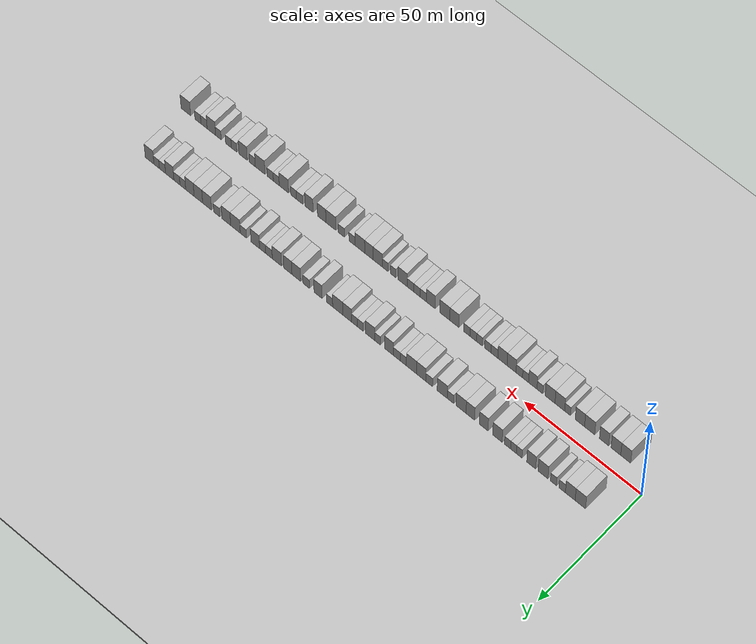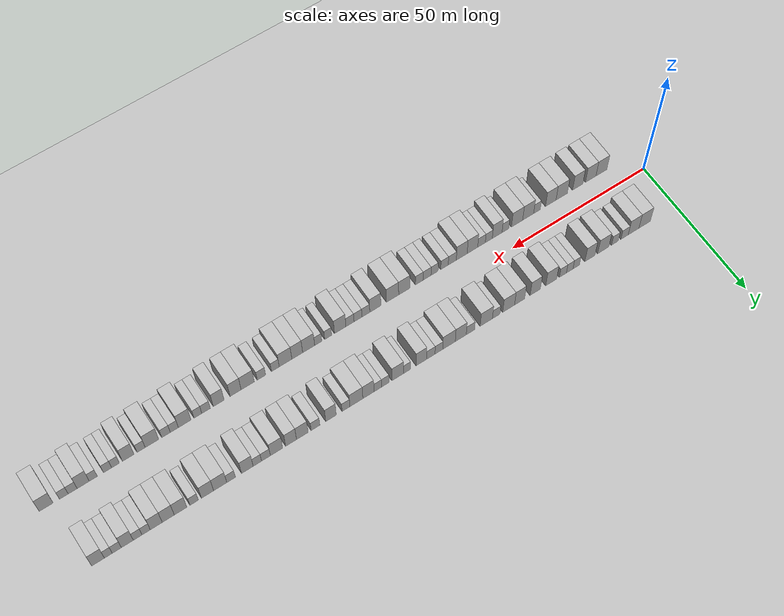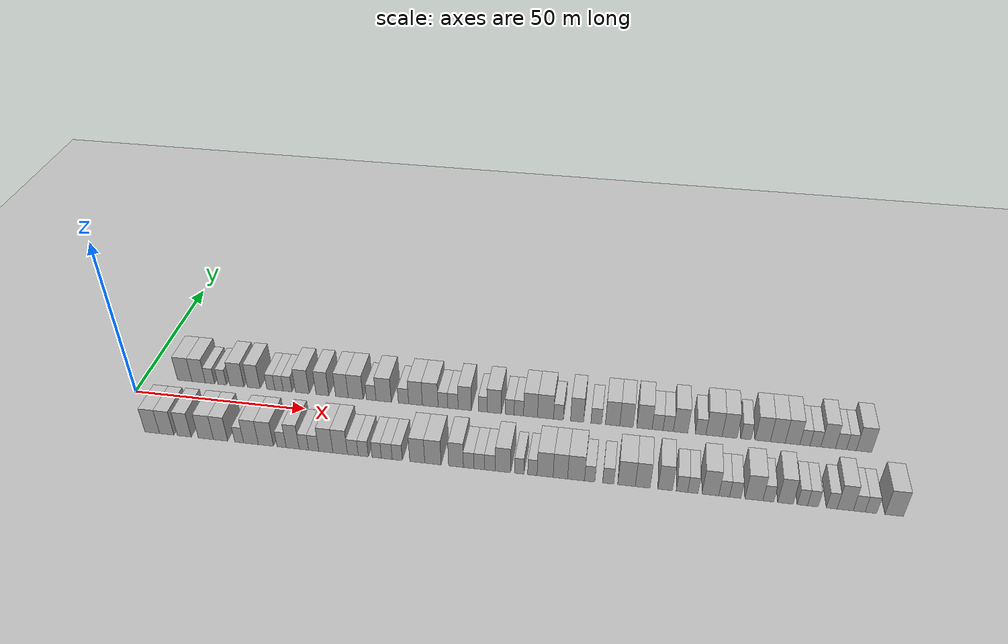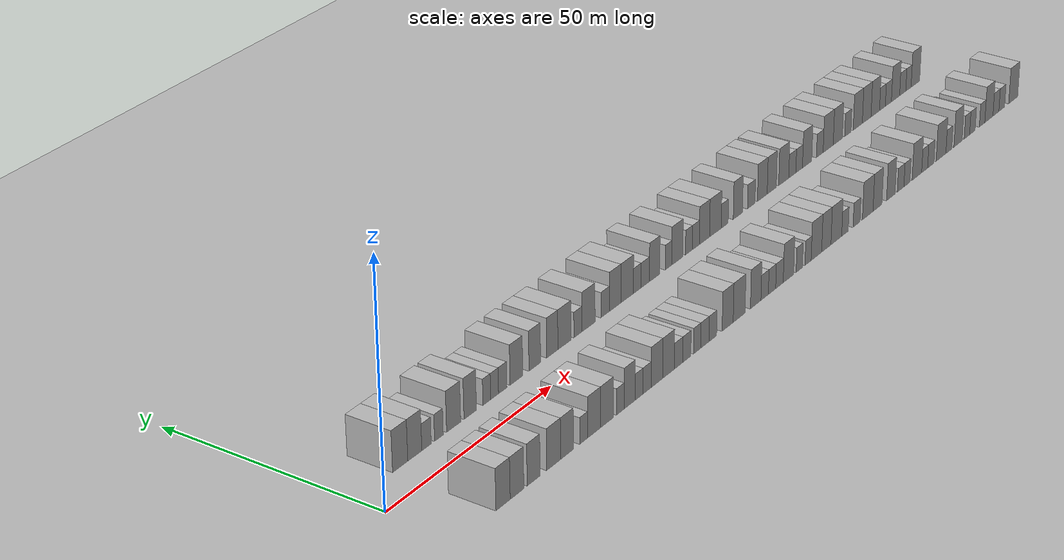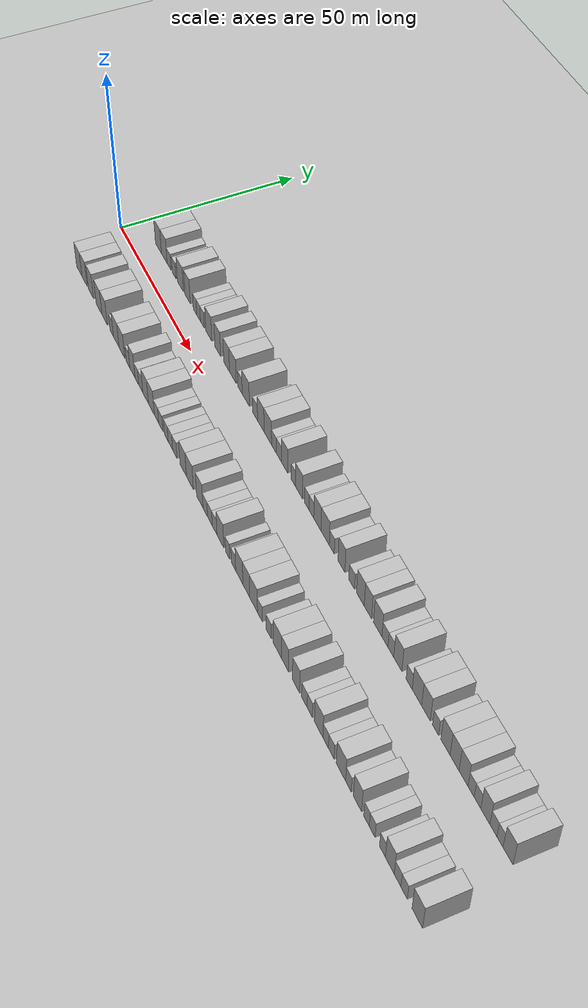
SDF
<?xml version="1.0" encoding="utf-8"?>

<sdf version="1.6">

   <world name="default">

      <gui fullscreen="0">

         <camera name="user_camera">

            <pose>-15 0 4.57585 0 0 0</pose>

            <view_controller>orbit</view_controller>

         </camera>

      </gui>

      <scene>

         <sky>

           <clouds>

             <speed>12</speed>

           </clouds>

         </sky>

         <ambient>0.4 0.4 0.4 1</ambient>

         <background>0.7 0.7 0.7 1</background>

         <shadows>1</shadows>

      </scene>

      <gravity>0 0 -9.8066</gravity>

      <magnetic_field>6e-06 2.3e-05 -4.2e-05</magnetic_field>

      <physics default="0" name="default_physics" type="ode">

         <ode>

            <solver>

               <type>quick</type>

               <iters>10</iters>

               <sor>1.0</sor>

               <use_dynamic_moi_rescaling>0</use_dynamic_moi_rescaling>

            </solver>

            <constraints>

               <cfm>0</cfm>

               <erp>0.2</erp>

               <contact_max_correcting_vel>100</contact_max_correcting_vel>

               <contact_surface_layer>0.001</contact_surface_layer>

            </constraints>

         </ode>

         <max_step_size>0.004</max_step_size>

         <real_time_factor>1</real_time_factor>

         <real_time_update_rate>250</real_time_update_rate>

      </physics>

      <light name="sun" type="directional">

         <cast_shadows>1</cast_shadows>

         <pose>0 0 10 0 0 0</pose>

         <diffuse>0.8 0.8 0.8 1</diffuse>

         <specular>0.2 0.2 0.2 1</specular>

         <attenuation>

            <range>1000</range>

            <constant>0.9</constant>

            <linear>0.01</linear>

            <quadratic>0.001</quadratic>

         </attenuation>

         <direction>-0.5 0.1 -0.9</direction>

      </light>

      <include>

         <name>ground_plane_1</name>

         <uri>model://HANNAS_ground_plane</uri>

         <pose>0 0 0  0 0 0</pose>

      </include>

      <include>

         <name>ground_plane_2</name>

         <uri>model://HANNAS_ground_plane</uri>

         <pose>100 0 0  0 0 0</pose>

      </include>

      <model name="building_1">

         <static>1</static>

         <pose frame="">12.1950 11.0000 0 0.000000 0.000000 1.570796</pose>

         <link name="link">

            <pose frame="">0 0 4.50 0 0 0</pose>

            <collision name="collision">

               <geometry>

                  <box>

                     <size>10.0000 4.3899 9.0000</size>

                  </box>

               </geometry>

               <max_contacts>10</max_contacts>

               <surface>

                  <contact>

                     <ode/>

                  </contact>

                  <bounce/>

                  <friction>

                     <torsional>

                        <ode/>

                     </torsional>

                     <ode/>

                  </friction>

               </surface>

            </collision>

            <visual name="visual">

               <cast_shadows>0</cast_shadows>

               <geometry>

                  <box>

                     <size>10.0000 4.3899 9.0000</size>

                  </box>

               </geometry>

               <material>

                  <script>

                     <uri>model://HANNAS_wall/materials/scripts</uri>

                     <uri>model://HANNAS_wall/materials/textures</uri>

                     <name>vrc/HANNAS_wall</name>

                  </script>

               </material>

            </visual>

            <self_collide>0</self_collide>

            <enable_wind>0</enable_wind>

            <kinematic>0</kinematic>

         </link>

      </model>

      <model name="building_2">

         <static>1</static>

         <pose frame="">16.4373 11.0000 0 0.000000 0.000000 1.570796</pose>

         <link name="link">

            <pose frame="">0 0 4.50 0 0 0</pose>

            <collision name="collision">

               <geometry>

                  <box>

                     <size>10.0000 4.0949 9.0000</size>

                  </box>

               </geometry>

               <max_contacts>10</max_contacts>

               <surface>

                  <contact>

                     <ode/>

                  </contact>

                  <bounce/>

                  <friction>

                     <torsional>

                        <ode/>

                     </torsional>

                     <ode/>

                  </friction>

               </surface>

            </collision>

            <visual name="visual">

               <cast_shadows>0</cast_shadows>

               <geometry>

                  <box>

                     <size>10.0000 4.0949 9.0000</size>

                  </box>

               </geometry>

               <material>

                  <script>

                     <uri>model://HANNAS_wall/materials/scripts</uri>

                     <uri>model://HANNAS_wall/materials/textures</uri>

                     <name>vrc/HANNAS_wall</name>

                  </script>

               </material>

            </visual>

            <self_collide>0</self_collide>

            <enable_wind>0</enable_wind>

            <kinematic>0</kinematic>

         </link>

      </model>

      <model name="building_3">

         <static>1</static>

         <pose frame="">19.8661 11.0000 0 0.000000 0.000000 1.570796</pose>

         <link name="link">

            <pose frame="">0 0 3.00 0 0 0</pose>

            <collision name="collision">

               <geometry>

                  <box>

                     <size>10.0000 2.7627 6.0000</size>

                  </box>

               </geometry>

               <max_contacts>10</max_contacts>

               <surface>

                  <contact>

                     <ode/>

                  </contact>

                  <bounce/>

                  <friction>

                     <torsional>

                        <ode/>

                     </torsional>

                     <ode/>

                  </friction>

               </surface>

            </collision>

            <visual name="visual">

               <cast_shadows>0</cast_shadows>

               <geometry>

                  <box>

                     <size>10.0000 2.7627 6.0000</size>

                  </box>

               </geometry>

               <material>

                  <script>

                     <uri>model://HANNAS_wall/materials/scripts</uri>

                     <uri>model://HANNAS_wall/materials/textures</uri>

                     <name>vrc/HANNAS_wall</name>

                  </script>

               </material>

            </visual>

            <self_collide>0</self_collide>

            <enable_wind>0</enable_wind>

            <kinematic>0</kinematic>

         </link>

      </model>

      <model name="building_4">

         <static>1</static>

         <pose frame="">23.5412 11.0000 0 0.000000 0.000000 1.570796</pose>

         <link name="link">

            <pose frame="">0 0 3.00 0 0 0</pose>

            <collision name="collision">

               <geometry>

                  <box>

                     <size>10.0000 2.5876 6.0000</size>

                  </box>

               </geometry>

               <max_contacts>10</max_contacts>

               <surface>

                  <contact>

                     <ode/>

                  </contact>

                  <bounce/>

                  <friction>

                     <torsional>

                        <ode/>

                     </torsional>

                     <ode/>

                  </friction>

               </surface>

            </collision>

            <visual name="visual">

               <cast_shadows>0</cast_shadows>

               <geometry>

                  <box>

                     <size>10.0000 2.5876 6.0000</size>

                  </box>

               </geometry>

               <material>

                  <script>

                     <uri>model://HANNAS_wall/materials/scripts</uri>

                     <uri>model://HANNAS_wall/materials/textures</uri>

                     <name>vrc/HANNAS_wall</name>

                  </script>

               </material>

            </visual>

            <self_collide>0</self_collide>

            <enable_wind>0</enable_wind>

            <kinematic>0</kinematic>

         </link>

      </model>

      <model name="building_5">

         <static>1</static>

         <pose frame="">27.9622 11.0000 0 0.000000 0.000000 1.570796</pose>

         <link name="link">

            <pose frame="">0 0 4.50 0 0 0</pose>

            <collision name="collision">

               <geometry>

                  <box>

                     <size>10.0000 4.2543 9.0000</size>

                  </box>

               </geometry>

               <max_contacts>10</max_contacts>

               <surface>

                  <contact>

                     <ode/>

                  </contact>

                  <bounce/>

                  <friction>

                     <torsional>

                        <ode/>

                     </torsional>

                     <ode/>

                  </friction>

               </surface>

            </collision>

            <visual name="visual">

               <cast_shadows>0</cast_shadows>

               <geometry>

                  <box>

                     <size>10.0000 4.2543 9.0000</size>

                  </box>

               </geometry>

               <material>

                  <script>

                     <uri>model://HANNAS_wall/materials/scripts</uri>

                     <uri>model://HANNAS_wall/materials/textures</uri>

                     <name>vrc/HANNAS_wall</name>

                  </script>

               </material>

            </visual>

            <self_collide>0</self_collide>

            <enable_wind>0</enable_wind>

            <kinematic>0</kinematic>

         </link>

      </model>

      <model name="building_6">

         <static>1</static>

         <pose frame="">32.9959 11.0000 0 0.000000 0.000000 1.570796</pose>

         <link name="link">

            <pose frame="">0 0 4.50 0 0 0</pose>

            <collision name="collision">

               <geometry>

                  <box>

                     <size>10.0000 3.8131 9.0000</size>

                  </box>

               </geometry>

               <max_contacts>10</max_contacts>

               <surface>

                  <contact>

                     <ode/>

                  </contact>

                  <bounce/>

                  <friction>

                     <torsional>

                        <ode/>

                     </torsional>

                     <ode/>

                  </friction>

               </surface>

            </collision>

            <visual name="visual">

               <cast_shadows>0</cast_shadows>

               <geometry>

                  <box>

                     <size>10.0000 3.8131 9.0000</size>

                  </box>

               </geometry>

               <material>

                  <script>

                     <uri>model://HANNAS_wall/materials/scripts</uri>

                     <uri>model://HANNAS_wall/materials/textures</uri>

                     <name>vrc/HANNAS_wall</name>

                  </script>

               </material>

            </visual>

            <self_collide>0</self_collide>

            <enable_wind>0</enable_wind>

            <kinematic>0</kinematic>

         </link>

      </model>

      <model name="building_7">

         <static>1</static>

         <pose frame="">38.1101 11.0000 0 0.000000 0.000000 1.570796</pose>

         <link name="link">

            <pose frame="">0 0 3.00 0 0 0</pose>

            <collision name="collision">

               <geometry>

                  <box>

                     <size>10.0000 2.4154 6.0000</size>

                  </box>

               </geometry>

               <max_contacts>10</max_contacts>

               <surface>

                  <contact>

                     <ode/>

                  </contact>

                  <bounce/>

                  <friction>

                     <torsional>

                        <ode/>

                     </torsional>

                     <ode/>

                  </friction>

               </surface>

            </collision>

            <visual name="visual">

               <cast_shadows>0</cast_shadows>

               <geometry>

                  <box>

                     <size>10.0000 2.4154 6.0000</size>

                  </box>

               </geometry>

               <material>

                  <script>

                     <uri>model://HANNAS_wall/materials/scripts</uri>

                     <uri>model://HANNAS_wall/materials/textures</uri>

                     <name>vrc/HANNAS_wall</name>

                  </script>

               </material>

            </visual>

            <self_collide>0</self_collide>

            <enable_wind>0</enable_wind>

            <kinematic>0</kinematic>

         </link>

      </model>

      <model name="building_8">

         <static>1</static>

         <pose frame="">40.5467 11.0000 0 0.000000 0.000000 1.570796</pose>

         <link name="link">

            <pose frame="">0 0 3.00 0 0 0</pose>

            <collision name="collision">

               <geometry>

                  <box>

                     <size>10.0000 2.4577 6.0000</size>

                  </box>

               </geometry>

               <max_contacts>10</max_contacts>

               <surface>

                  <contact>

                     <ode/>

                  </contact>

                  <bounce/>

                  <friction>

                     <torsional>

                        <ode/>

                     </torsional>

                     <ode/>

                  </friction>

               </surface>

            </collision>

            <visual name="visual">

               <cast_shadows>0</cast_shadows>

               <geometry>

                  <box>

                     <size>10.0000 2.4577 6.0000</size>

                  </box>

               </geometry>

               <material>

                  <script>

                     <uri>model://HANNAS_wall/materials/scripts</uri>

                     <uri>model://HANNAS_wall/materials/textures</uri>

                     <name>vrc/HANNAS_wall</name>

                  </script>

               </material>

            </visual>

            <self_collide>0</self_collide>

            <enable_wind>0</enable_wind>

            <kinematic>0</kinematic>

         </link>

      </model>

      <model name="building_9">

         <static>1</static>

         <pose frame="">43.0879 11.0000 0 0.000000 0.000000 1.570796</pose>

         <link name="link">

            <pose frame="">0 0 3.00 0 0 0</pose>

            <collision name="collision">

               <geometry>

                  <box>

                     <size>10.0000 2.6247 6.0000</size>

                  </box>

               </geometry>

               <max_contacts>10</max_contacts>

               <surface>

                  <contact>

                     <ode/>

                  </contact>

                  <bounce/>

                  <friction>

                     <torsional>

                        <ode/>

                     </torsional>

                     <ode/>

                  </friction>

               </surface>

            </collision>

            <visual name="visual">

               <cast_shadows>0</cast_shadows>

               <geometry>

                  <box>

                     <size>10.0000 2.6247 6.0000</size>

                  </box>

               </geometry>

               <material>

                  <script>

                     <uri>model://HANNAS_wall/materials/scripts</uri>

                     <uri>model://HANNAS_wall/materials/textures</uri>

                     <name>vrc/HANNAS_wall</name>

                  </script>

               </material>

            </visual>

            <self_collide>0</self_collide>

            <enable_wind>0</enable_wind>

            <kinematic>0</kinematic>

         </link>

      </model>

      <model name="building_10">

         <static>1</static>

         <pose frame="">47.4309 11.0000 0 0.000000 0.000000 1.570796</pose>

         <link name="link">

            <pose frame="">0 0 4.50 0 0 0</pose>

            <collision name="collision">

               <geometry>

                  <box>

                     <size>10.0000 4.0614 9.0000</size>

                  </box>

               </geometry>

               <max_contacts>10</max_contacts>

               <surface>

                  <contact>

                     <ode/>

                  </contact>

                  <bounce/>

                  <friction>

                     <torsional>

                        <ode/>

                     </torsional>

                     <ode/>

                  </friction>

               </surface>

            </collision>

            <visual name="visual">

               <cast_shadows>0</cast_shadows>

               <geometry>

                  <box>

                     <size>10.0000 4.0614 9.0000</size>

                  </box>

               </geometry>

               <material>

                  <script>

                     <uri>model://HANNAS_wall/materials/scripts</uri>

                     <uri>model://HANNAS_wall/materials/textures</uri>

                     <name>vrc/HANNAS_wall</name>

                  </script>

               </material>

            </visual>

            <self_collide>0</self_collide>

            <enable_wind>0</enable_wind>

            <kinematic>0</kinematic>

         </link>

      </model>

      <model name="building_11">

         <static>1</static>

         <pose frame="">53.3396 11.0000 0 0.000000 0.000000 1.570796</pose>

         <link name="link">

            <pose frame="">0 0 4.50 0 0 0</pose>

            <collision name="collision">

               <geometry>

                  <box>

                     <size>10.0000 3.7560 9.0000</size>

                  </box>

               </geometry>

               <max_contacts>10</max_contacts>

               <surface>

                  <contact>

                     <ode/>

                  </contact>

                  <bounce/>

                  <friction>

                     <torsional>

                        <ode/>

                     </torsional>

                     <ode/>

                  </friction>

               </surface>

            </collision>

            <visual name="visual">

               <cast_shadows>0</cast_shadows>

               <geometry>

                  <box>

                     <size>10.0000 3.7560 9.0000</size>

                  </box>

               </geometry>

               <material>

                  <script>

                     <uri>model://HANNAS_wall/materials/scripts</uri>

                     <uri>model://HANNAS_wall/materials/textures</uri>

                     <name>vrc/HANNAS_wall</name>

                  </script>

               </material>

            </visual>

            <self_collide>0</self_collide>

            <enable_wind>0</enable_wind>

            <kinematic>0</kinematic>

         </link>

      </model>

      <model name="building_12">

         <static>1</static>

         <pose frame="">59.0669 11.0000 0 0.000000 0.000000 1.570796</pose>

         <link name="link">

            <pose frame="">0 0 4.50 0 0 0</pose>

            <collision name="collision">

               <geometry>

                  <box>

                     <size>10.0000 3.6986 9.0000</size>

                  </box>

               </geometry>

               <max_contacts>10</max_contacts>

               <surface>

                  <contact>

                     <ode/>

                  </contact>

                  <bounce/>

                  <friction>

                     <torsional>

                        <ode/>

                     </torsional>

                     <ode/>

                  </friction>

               </surface>

            </collision>

            <visual name="visual">

               <cast_shadows>0</cast_shadows>

               <geometry>

                  <box>

                     <size>10.0000 3.6986 9.0000</size>

                  </box>

               </geometry>

               <material>

                  <script>

                     <uri>model://HANNAS_wall/materials/scripts</uri>

                     <uri>model://HANNAS_wall/materials/textures</uri>

                     <name>vrc/HANNAS_wall</name>

                  </script>

               </material>

            </visual>

            <self_collide>0</self_collide>

            <enable_wind>0</enable_wind>

            <kinematic>0</kinematic>

         </link>

      </model>

      <model name="building_13">

         <static>1</static>

         <pose frame="">63.0812 11.0000 0 0.000000 0.000000 1.570796</pose>

         <link name="link">

            <pose frame="">0 0 4.50 0 0 0</pose>

            <collision name="collision">

               <geometry>

                  <box>

                     <size>10.0000 4.3301 9.0000</size>

                  </box>

               </geometry>

               <max_contacts>10</max_contacts>

               <surface>

                  <contact>

                     <ode/>

                  </contact>

                  <bounce/>

                  <friction>

                     <torsional>

                        <ode/>

                     </torsional>

                     <ode/>

                  </friction>

               </surface>

            </collision>

            <visual name="visual">

               <cast_shadows>0</cast_shadows>

               <geometry>

                  <box>

                     <size>10.0000 4.3301 9.0000</size>

                  </box>

               </geometry>

               <material>

                  <script>

                     <uri>model://HANNAS_wall/materials/scripts</uri>

                     <uri>model://HANNAS_wall/materials/textures</uri>

                     <name>vrc/HANNAS_wall</name>

                  </script>

               </material>

            </visual>

            <self_collide>0</self_collide>

            <enable_wind>0</enable_wind>

            <kinematic>0</kinematic>

         </link>

      </model>

      <model name="building_14">

         <static>1</static>

         <pose frame="">67.6097 11.0000 0 0.000000 0.000000 1.570796</pose>

         <link name="link">

            <pose frame="">0 0 3.00 0 0 0</pose>

            <collision name="collision">

               <geometry>

                  <box>

                     <size>10.0000 2.7268 6.0000</size>

                  </box>

               </geometry>

               <max_contacts>10</max_contacts>

               <surface>

                  <contact>

                     <ode/>

                  </contact>

                  <bounce/>

                  <friction>

                     <torsional>

                        <ode/>

                     </torsional>

                     <ode/>

                  </friction>

               </surface>

            </collision>

            <visual name="visual">

               <cast_shadows>0</cast_shadows>

               <geometry>

                  <box>

                     <size>10.0000 2.7268 6.0000</size>

                  </box>

               </geometry>

               <material>

                  <script>

                     <uri>model://HANNAS_wall/materials/scripts</uri>

                     <uri>model://HANNAS_wall/materials/textures</uri>

                     <name>vrc/HANNAS_wall</name>

                  </script>

               </material>

            </visual>

            <self_collide>0</self_collide>

            <enable_wind>0</enable_wind>

            <kinematic>0</kinematic>

         </link>

      </model>

      <model name="building_15">

         <static>1</static>

         <pose frame="">71.1971 11.0000 0 0.000000 0.000000 1.570796</pose>

         <link name="link">

            <pose frame="">0 0 4.50 0 0 0</pose>

            <collision name="collision">

               <geometry>

                  <box>

                     <size>10.0000 4.4480 9.0000</size>

                  </box>

               </geometry>

               <max_contacts>10</max_contacts>

               <surface>

                  <contact>

                     <ode/>

                  </contact>

                  <bounce/>

                  <friction>

                     <torsional>

                        <ode/>

                     </torsional>

                     <ode/>

                  </friction>

               </surface>

            </collision>

            <visual name="visual">

               <cast_shadows>0</cast_shadows>

               <geometry>

                  <box>

                     <size>10.0000 4.4480 9.0000</size>

                  </box>

               </geometry>

               <material>

                  <script>

                     <uri>model://HANNAS_wall/materials/scripts</uri>

                     <uri>model://HANNAS_wall/materials/textures</uri>

                     <name>vrc/HANNAS_wall</name>

                  </script>

               </material>

            </visual>

            <self_collide>0</self_collide>

            <enable_wind>0</enable_wind>

            <kinematic>0</kinematic>

         </link>

      </model>

      <model name="building_16">

         <static>1</static>

         <pose frame="">76.9208 11.0000 0 0.000000 0.000000 1.570796</pose>

         <link name="link">

            <pose frame="">0 0 3.00 0 0 0</pose>

            <collision name="collision">

               <geometry>

                  <box>

                     <size>10.0000 2.9993 6.0000</size>

                  </box>

               </geometry>

               <max_contacts>10</max_contacts>

               <surface>

                  <contact>

                     <ode/>

                  </contact>

                  <bounce/>

                  <friction>

                     <torsional>

                        <ode/>

                     </torsional>

                     <ode/>

                  </friction>

               </surface>

            </collision>

            <visual name="visual">

               <cast_shadows>0</cast_shadows>

               <geometry>

                  <box>

                     <size>10.0000 2.9993 6.0000</size>

                  </box>

               </geometry>

               <material>

                  <script>

                     <uri>model://HANNAS_wall/materials/scripts</uri>

                     <uri>model://HANNAS_wall/materials/textures</uri>

                     <name>vrc/HANNAS_wall</name>

                  </script>

               </material>

            </visual>

            <self_collide>0</self_collide>

            <enable_wind>0</enable_wind>

            <kinematic>0</kinematic>

         </link>

      </model>

      <model name="building_17">

         <static>1</static>

         <pose frame="">80.3822 11.0000 0 0.000000 0.000000 1.570796</pose>

         <link name="link">

            <pose frame="">0 0 4.50 0 0 0</pose>

            <collision name="collision">

               <geometry>

                  <box>

                     <size>10.0000 3.9234 9.0000</size>

                  </box>

               </geometry>

               <max_contacts>10</max_contacts>

               <surface>

                  <contact>

                     <ode/>

                  </contact>

                  <bounce/>

                  <friction>

                     <torsional>

                        <ode/>

                     </torsional>

                     <ode/>

                  </friction>

               </surface>

            </collision>

            <visual name="visual">

               <cast_shadows>0</cast_shadows>

               <geometry>

                  <box>

                     <size>10.0000 3.9234 9.0000</size>

                  </box>

               </geometry>

               <material>

                  <script>

                     <uri>model://HANNAS_wall/materials/scripts</uri>

                     <uri>model://HANNAS_wall/materials/textures</uri>

                     <name>vrc/HANNAS_wall</name>

                  </script>

               </material>

            </visual>

            <self_collide>0</self_collide>

            <enable_wind>0</enable_wind>

            <kinematic>0</kinematic>

         </link>

      </model>

      <model name="building_18">

         <static>1</static>

         <pose frame="">84.5905 11.0000 0 0.000000 0.000000 1.570796</pose>

         <link name="link">

            <pose frame="">0 0 4.50 0 0 0</pose>

            <collision name="collision">

               <geometry>

                  <box>

                     <size>10.0000 4.4931 9.0000</size>

                  </box>

               </geometry>

               <max_contacts>10</max_contacts>

               <surface>

                  <contact>

                     <ode/>

                  </contact>

                  <bounce/>

                  <friction>

                     <torsional>

                        <ode/>

                     </torsional>

                     <ode/>

                  </friction>

               </surface>

            </collision>

            <visual name="visual">

               <cast_shadows>0</cast_shadows>

               <geometry>

                  <box>

                     <size>10.0000 4.4931 9.0000</size>

                  </box>

               </geometry>

               <material>

                  <script>

                     <uri>model://HANNAS_wall/materials/scripts</uri>

                     <uri>model://HANNAS_wall/materials/textures</uri>

                     <name>vrc/HANNAS_wall</name>

                  </script>

               </material>

            </visual>

            <self_collide>0</self_collide>

            <enable_wind>0</enable_wind>

            <kinematic>0</kinematic>

         </link>

      </model>

      <model name="building_19">

         <static>1</static>

         <pose frame="">88.2028 11.0000 0 0.000000 0.000000 1.570796</pose>

         <link name="link">

            <pose frame="">0 0 3.00 0 0 0</pose>

            <collision name="collision">

               <geometry>

                  <box>

                     <size>10.0000 2.7315 6.0000</size>

                  </box>

               </geometry>

               <max_contacts>10</max_contacts>

               <surface>

                  <contact>

                     <ode/>

                  </contact>

                  <bounce/>

                  <friction>

                     <torsional>

                        <ode/>

                     </torsional>

                     <ode/>

                  </friction>

               </surface>

            </collision>

            <visual name="visual">

               <cast_shadows>0</cast_shadows>

               <geometry>

                  <box>

                     <size>10.0000 2.7315 6.0000</size>

                  </box>

               </geometry>

               <material>

                  <script>

                     <uri>model://HANNAS_wall/materials/scripts</uri>

                     <uri>model://HANNAS_wall/materials/textures</uri>

                     <name>vrc/HANNAS_wall</name>

                  </script>

               </material>

            </visual>

            <self_collide>0</self_collide>

            <enable_wind>0</enable_wind>

            <kinematic>0</kinematic>

         </link>

      </model>

      <model name="building_20">

         <static>1</static>

         <pose frame="">91.0572 11.0000 0 0.000000 0.000000 1.570796</pose>

         <link name="link">

            <pose frame="">0 0 3.00 0 0 0</pose>

            <collision name="collision">

               <geometry>

                  <box>

                     <size>10.0000 2.9773 6.0000</size>

                  </box>

               </geometry>

               <max_contacts>10</max_contacts>

               <surface>

                  <contact>

                     <ode/>

                  </contact>

                  <bounce/>

                  <friction>

                     <torsional>

                        <ode/>

                     </torsional>

                     <ode/>

                  </friction>

               </surface>

            </collision>

            <visual name="visual">

               <cast_shadows>0</cast_shadows>

               <geometry>

                  <box>

                     <size>10.0000 2.9773 6.0000</size>

                  </box>

               </geometry>

               <material>

                  <script>

                     <uri>model://HANNAS_wall/materials/scripts</uri>

                     <uri>model://HANNAS_wall/materials/textures</uri>

                     <name>vrc/HANNAS_wall</name>

                  </script>

               </material>

            </visual>

            <self_collide>0</self_collide>

            <enable_wind>0</enable_wind>

            <kinematic>0</kinematic>

         </link>

      </model>

      <model name="building_21">

         <static>1</static>

         <pose frame="">94.4066 11.0000 0 0.000000 0.000000 1.570796</pose>

         <link name="link">

            <pose frame="">0 0 4.50 0 0 0</pose>

            <collision name="collision">

               <geometry>

                  <box>

                     <size>10.0000 3.7216 9.0000</size>

                  </box>

               </geometry>

               <max_contacts>10</max_contacts>

               <surface>

                  <contact>

                     <ode/>

                  </contact>

                  <bounce/>

                  <friction>

                     <torsional>

                        <ode/>

                     </torsional>

                     <ode/>

                  </friction>

               </surface>

            </collision>

            <visual name="visual">

               <cast_shadows>0</cast_shadows>

               <geometry>

                  <box>

                     <size>10.0000 3.7216 9.0000</size>

                  </box>

               </geometry>

               <material>

                  <script>

                     <uri>model://HANNAS_wall/materials/scripts</uri>

                     <uri>model://HANNAS_wall/materials/textures</uri>

                     <name>vrc/HANNAS_wall</name>

                  </script>

               </material>

            </visual>

            <self_collide>0</self_collide>

            <enable_wind>0</enable_wind>

            <kinematic>0</kinematic>

         </link>

      </model>

      <model name="building_22">

         <static>1</static>

         <pose frame="">99.4775 11.0000 0 0.000000 0.000000 1.570796</pose>

         <link name="link">

            <pose frame="">0 0 3.00 0 0 0</pose>

            <collision name="collision">

               <geometry>

                  <box>

                     <size>10.0000 2.4202 6.0000</size>

                  </box>

               </geometry>

               <max_contacts>10</max_contacts>

               <surface>

                  <contact>

                     <ode/>

                  </contact>

                  <bounce/>

                  <friction>

                     <torsional>

                        <ode/>

                     </torsional>

                     <ode/>

                  </friction>

               </surface>

            </collision>

            <visual name="visual">

               <cast_shadows>0</cast_shadows>

               <geometry>

                  <box>

                     <size>10.0000 2.4202 6.0000</size>

                  </box>

               </geometry>

               <material>

                  <script>

                     <uri>model://HANNAS_wall/materials/scripts</uri>

                     <uri>model://HANNAS_wall/materials/textures</uri>

                     <name>vrc/HANNAS_wall</name>

                  </script>

               </material>

            </visual>

            <self_collide>0</self_collide>

            <enable_wind>0</enable_wind>

            <kinematic>0</kinematic>

         </link>

      </model>

      <model name="building_23">

         <static>1</static>

         <pose frame="">102.7221 11.0000 0 0.000000 0.000000 1.570796</pose>

         <link name="link">

            <pose frame="">0 0 4.50 0 0 0</pose>

            <collision name="collision">

               <geometry>

                  <box>

                     <size>10.0000 4.0689 9.0000</size>

                  </box>

               </geometry>

               <max_contacts>10</max_contacts>

               <surface>

                  <contact>

                     <ode/>

                  </contact>

                  <bounce/>

                  <friction>

                     <torsional>

                        <ode/>

                     </torsional>

                     <ode/>

                  </friction>

               </surface>

            </collision>

            <visual name="visual">

               <cast_shadows>0</cast_shadows>

               <geometry>

                  <box>

                     <size>10.0000 4.0689 9.0000</size>

                  </box>

               </geometry>

               <material>

                  <script>

                     <uri>model://HANNAS_wall/materials/scripts</uri>

                     <uri>model://HANNAS_wall/materials/textures</uri>

                     <name>vrc/HANNAS_wall</name>

                  </script>

               </material>

            </visual>

            <self_collide>0</self_collide>

            <enable_wind>0</enable_wind>

            <kinematic>0</kinematic>

         </link>

      </model>

      <model name="building_24">

         <static>1</static>

         <pose frame="">107.0462 11.0000 0 0.000000 0.000000 1.570796</pose>

         <link name="link">

            <pose frame="">0 0 3.00 0 0 0</pose>

            <collision name="collision">

               <geometry>

                  <box>

                     <size>10.0000 2.5793 6.0000</size>

                  </box>

               </geometry>

               <max_contacts>10</max_contacts>

               <surface>

                  <contact>

                     <ode/>

                  </contact>

                  <bounce/>

                  <friction>

                     <torsional>

                        <ode/>

                     </torsional>

                     <ode/>

                  </friction>

               </surface>

            </collision>

            <visual name="visual">

               <cast_shadows>0</cast_shadows>

               <geometry>

                  <box>

                     <size>10.0000 2.5793 6.0000</size>

                  </box>

               </geometry>

               <material>

                  <script>

                     <uri>model://HANNAS_wall/materials/scripts</uri>

                     <uri>model://HANNAS_wall/materials/textures</uri>

                     <name>vrc/HANNAS_wall</name>

                  </script>

               </material>

            </visual>

            <self_collide>0</self_collide>

            <enable_wind>0</enable_wind>

            <kinematic>0</kinematic>

         </link>

      </model>

      <model name="building_25">

         <static>1</static>

         <pose frame="">109.6447 11.0000 0 0.000000 0.000000 1.570796</pose>

         <link name="link">

            <pose frame="">0 0 3.00 0 0 0</pose>

            <collision name="collision">

               <geometry>

                  <box>

                     <size>10.0000 2.6178 6.0000</size>

                  </box>

               </geometry>

               <max_contacts>10</max_contacts>

               <surface>

                  <contact>

                     <ode/>

                  </contact>

                  <bounce/>

                  <friction>

                     <torsional>

                        <ode/>

                     </torsional>

                     <ode/>

                  </friction>

               </surface>

            </collision>

            <visual name="visual">

               <cast_shadows>0</cast_shadows>

               <geometry>

                  <box>

                     <size>10.0000 2.6178 6.0000</size>

                  </box>

               </geometry>

               <material>

                  <script>

                     <uri>model://HANNAS_wall/materials/scripts</uri>

                     <uri>model://HANNAS_wall/materials/textures</uri>

                     <name>vrc/HANNAS_wall</name>

                  </script>

               </material>

            </visual>

            <self_collide>0</self_collide>

            <enable_wind>0</enable_wind>

            <kinematic>0</kinematic>

         </link>

      </model>

      <model name="building_26">

         <static>1</static>

         <pose frame="">112.9036 11.0000 0 0.000000 0.000000 1.570796</pose>

         <link name="link">

            <pose frame="">0 0 4.50 0 0 0</pose>

            <collision name="collision">

               <geometry>

                  <box>

                     <size>10.0000 3.9001 9.0000</size>

                  </box>

               </geometry>

               <max_contacts>10</max_contacts>

               <surface>

                  <contact>

                     <ode/>

                  </contact>

                  <bounce/>

                  <friction>

                     <torsional>

                        <ode/>

                     </torsional>

                     <ode/>

                  </friction>

               </surface>

            </collision>

            <visual name="visual">

               <cast_shadows>0</cast_shadows>

               <geometry>

                  <box>

                     <size>10.0000 3.9001 9.0000</size>

                  </box>

               </geometry>

               <material>

                  <script>

                     <uri>model://HANNAS_wall/materials/scripts</uri>

                     <uri>model://HANNAS_wall/materials/textures</uri>

                     <name>vrc/HANNAS_wall</name>

                  </script>

               </material>

            </visual>

            <self_collide>0</self_collide>

            <enable_wind>0</enable_wind>

            <kinematic>0</kinematic>

         </link>

      </model>

      <model name="building_27">

         <static>1</static>

         <pose frame="">117.0873 11.0000 0 0.000000 0.000000 1.570796</pose>

         <link name="link">

            <pose frame="">0 0 4.50 0 0 0</pose>

            <collision name="collision">

               <geometry>

                  <box>

                     <size>10.0000 4.4672 9.0000</size>

                  </box>

               </geometry>

               <max_contacts>10</max_contacts>

               <surface>

                  <contact>

                     <ode/>

                  </contact>

                  <bounce/>

                  <friction>

                     <torsional>

                        <ode/>

                     </torsional>

                     <ode/>

                  </friction>

               </surface>

            </collision>

            <visual name="visual">

               <cast_shadows>0</cast_shadows>

               <geometry>

                  <box>

                     <size>10.0000 4.4672 9.0000</size>

                  </box>

               </geometry>

               <material>

                  <script>

                     <uri>model://HANNAS_wall/materials/scripts</uri>

                     <uri>model://HANNAS_wall/materials/textures</uri>

                     <name>vrc/HANNAS_wall</name>

                  </script>

               </material>

            </visual>

            <self_collide>0</self_collide>

            <enable_wind>0</enable_wind>

            <kinematic>0</kinematic>

         </link>

      </model>

      <model name="building_28">

         <static>1</static>

         <pose frame="">120.6604 11.0000 0 0.000000 0.000000 1.570796</pose>

         <link name="link">

            <pose frame="">0 0 3.00 0 0 0</pose>

            <collision name="collision">

               <geometry>

                  <box>

                     <size>10.0000 2.6791 6.0000</size>

                  </box>

               </geometry>

               <max_contacts>10</max_contacts>

               <surface>

                  <contact>

                     <ode/>

                  </contact>

                  <bounce/>

                  <friction>

                     <torsional>

                        <ode/>

                     </torsional>

                     <ode/>

                  </friction>

               </surface>

            </collision>

            <visual name="visual">

               <cast_shadows>0</cast_shadows>

               <geometry>

                  <box>

                     <size>10.0000 2.6791 6.0000</size>

                  </box>

               </geometry>

               <material>

                  <script>

                     <uri>model://HANNAS_wall/materials/scripts</uri>

                     <uri>model://HANNAS_wall/materials/textures</uri>

                     <name>vrc/HANNAS_wall</name>

                  </script>

               </material>

            </visual>

            <self_collide>0</self_collide>

            <enable_wind>0</enable_wind>

            <kinematic>0</kinematic>

         </link>

      </model>

      <model name="building_29">

         <static>1</static>

         <pose frame="">125.8022 11.0000 0 0.000000 0.000000 1.570796</pose>

         <link name="link">

            <pose frame="">0 0 4.50 0 0 0</pose>

            <collision name="collision">

               <geometry>

                  <box>

                     <size>10.0000 3.6045 9.0000</size>

                  </box>

               </geometry>

               <max_contacts>10</max_contacts>

               <surface>

                  <contact>

                     <ode/>

                  </contact>

                  <bounce/>

                  <friction>

                     <torsional>

                        <ode/>

                     </torsional>

                     <ode/>

                  </friction>

               </surface>

            </collision>

            <visual name="visual">

               <cast_shadows>0</cast_shadows>

               <geometry>

                  <box>

                     <size>10.0000 3.6045 9.0000</size>

                  </box>

               </geometry>

               <material>

                  <script>

                     <uri>model://HANNAS_wall/materials/scripts</uri>

                     <uri>model://HANNAS_wall/materials/textures</uri>

                     <name>vrc/HANNAS_wall</name>

                  </script>

               </material>

            </visual>

            <self_collide>0</self_collide>

            <enable_wind>0</enable_wind>

            <kinematic>0</kinematic>

         </link>

      </model>

      <model name="building_30">

         <static>1</static>

         <pose frame="">131.0874 11.0000 0 0.000000 0.000000 1.570796</pose>

         <link name="link">

            <pose frame="">0 0 3.00 0 0 0</pose>

            <collision name="collision">

               <geometry>

                  <box>

                     <size>10.0000 2.9658 6.0000</size>

                  </box>

               </geometry>

               <max_contacts>10</max_contacts>

               <surface>

                  <contact>

                     <ode/>

                  </contact>

                  <bounce/>

                  <friction>

                     <torsional>

                        <ode/>

                     </torsional>

                     <ode/>

                  </friction>

               </surface>

            </collision>

            <visual name="visual">

               <cast_shadows>0</cast_shadows>

               <geometry>

                  <box>

                     <size>10.0000 2.9658 6.0000</size>

                  </box>

               </geometry>

               <material>

                  <script>

                     <uri>model://HANNAS_wall/materials/scripts</uri>

                     <uri>model://HANNAS_wall/materials/textures</uri>

                     <name>vrc/HANNAS_wall</name>

                  </script>

               </material>

            </visual>

            <self_collide>0</self_collide>

            <enable_wind>0</enable_wind>

            <kinematic>0</kinematic>

         </link>

      </model>

      <model name="building_31">

         <static>1</static>

         <pose frame="">135.5373 11.0000 0 0.000000 0.000000 1.570796</pose>

         <link name="link">

            <pose frame="">0 0 4.50 0 0 0</pose>

            <collision name="collision">

               <geometry>

                  <box>

                     <size>10.0000 3.9340 9.0000</size>

                  </box>

               </geometry>

               <max_contacts>10</max_contacts>

               <surface>

                  <contact>

                     <ode/>

                  </contact>

                  <bounce/>

                  <friction>

                     <torsional>

                        <ode/>

                     </torsional>

                     <ode/>

                  </friction>

               </surface>

            </collision>

            <visual name="visual">

               <cast_shadows>0</cast_shadows>

               <geometry>

                  <box>

                     <size>10.0000 3.9340 9.0000</size>

                  </box>

               </geometry>

               <material>

                  <script>

                     <uri>model://HANNAS_wall/materials/scripts</uri>

                     <uri>model://HANNAS_wall/materials/textures</uri>

                     <name>vrc/HANNAS_wall</name>

                  </script>

               </material>

            </visual>

            <self_collide>0</self_collide>

            <enable_wind>0</enable_wind>

            <kinematic>0</kinematic>

         </link>

      </model>

      <model name="building_32">

         <static>1</static>

         <pose frame="">139.3370 11.0000 0 0.000000 0.000000 1.570796</pose>

         <link name="link">

            <pose frame="">0 0 4.50 0 0 0</pose>

            <collision name="collision">

               <geometry>

                  <box>

                     <size>10.0000 3.6655 9.0000</size>

                  </box>

               </geometry>

               <max_contacts>10</max_contacts>

               <surface>

                  <contact>

                     <ode/>

                  </contact>

                  <bounce/>

                  <friction>

                     <torsional>

                        <ode/>

                     </torsional>

                     <ode/>

                  </friction>

               </surface>

            </collision>

            <visual name="visual">

               <cast_shadows>0</cast_shadows>

               <geometry>

                  <box>

                     <size>10.0000 3.6655 9.0000</size>

                  </box>

               </geometry>

               <material>

                  <script>

                     <uri>model://HANNAS_wall/materials/scripts</uri>

                     <uri>model://HANNAS_wall/materials/textures</uri>

                     <name>vrc/HANNAS_wall</name>

                  </script>

               </material>

            </visual>

            <self_collide>0</self_collide>

            <enable_wind>0</enable_wind>

            <kinematic>0</kinematic>

         </link>

      </model>

      <model name="building_33">

         <static>1</static>

         <pose frame="">144.2368 11.0000 0 0.000000 0.000000 1.570796</pose>

         <link name="link">

            <pose frame="">0 0 4.50 0 0 0</pose>

            <collision name="collision">

               <geometry>

                  <box>

                     <size>10.0000 4.1340 9.0000</size>

                  </box>

               </geometry>

               <max_contacts>10</max_contacts>

               <surface>

                  <contact>

                     <ode/>

                  </contact>

                  <bounce/>

                  <friction>

                     <torsional>

                        <ode/>

                     </torsional>

                     <ode/>

                  </friction>

               </surface>

            </collision>

            <visual name="visual">

               <cast_shadows>0</cast_shadows>

               <geometry>

                  <box>

                     <size>10.0000 4.1340 9.0000</size>

                  </box>

               </geometry>

               <material>

                  <script>

                     <uri>model://HANNAS_wall/materials/scripts</uri>

                     <uri>model://HANNAS_wall/materials/textures</uri>

                     <name>vrc/HANNAS_wall</name>

                  </script>

               </material>

            </visual>

            <self_collide>0</self_collide>

            <enable_wind>0</enable_wind>

            <kinematic>0</kinematic>

         </link>

      </model>

      <model name="building_34">

         <static>1</static>

         <pose frame="">147.7843 11.0000 0 0.000000 0.000000 1.570796</pose>

         <link name="link">

            <pose frame="">0 0 3.00 0 0 0</pose>

            <collision name="collision">

               <geometry>

                  <box>

                     <size>10.0000 2.9610 6.0000</size>

                  </box>

               </geometry>

               <max_contacts>10</max_contacts>

               <surface>

                  <contact>

                     <ode/>

                  </contact>

                  <bounce/>

                  <friction>

                     <torsional>

                        <ode/>

                     </torsional>

                     <ode/>

                  </friction>

               </surface>

            </collision>

            <visual name="visual">

               <cast_shadows>0</cast_shadows>

               <geometry>

                  <box>

                     <size>10.0000 2.9610 6.0000</size>

                  </box>

               </geometry>

               <material>

                  <script>

                     <uri>model://HANNAS_wall/materials/scripts</uri>

                     <uri>model://HANNAS_wall/materials/textures</uri>

                     <name>vrc/HANNAS_wall</name>

                  </script>

               </material>

            </visual>

            <self_collide>0</self_collide>

            <enable_wind>0</enable_wind>

            <kinematic>0</kinematic>

         </link>

      </model>

      <model name="building_35">

         <static>1</static>

         <pose frame="">150.6459 11.0000 0 0.000000 0.000000 1.570796</pose>

         <link name="link">

            <pose frame="">0 0 3.00 0 0 0</pose>

            <collision name="collision">

               <geometry>

                  <box>

                     <size>10.0000 2.7623 6.0000</size>

                  </box>

               </geometry>

               <max_contacts>10</max_contacts>

               <surface>

                  <contact>

                     <ode/>

                  </contact>

                  <bounce/>

                  <friction>

                     <torsional>

                        <ode/>

                     </torsional>

                     <ode/>

                  </friction>

               </surface>

            </collision>

            <visual name="visual">

               <cast_shadows>0</cast_shadows>

               <geometry>

                  <box>

                     <size>10.0000 2.7623 6.0000</size>

                  </box>

               </geometry>

               <material>

                  <script>

                     <uri>model://HANNAS_wall/materials/scripts</uri>

                     <uri>model://HANNAS_wall/materials/textures</uri>

                     <name>vrc/HANNAS_wall</name>

                  </script>

               </material>

            </visual>

            <self_collide>0</self_collide>

            <enable_wind>0</enable_wind>

            <kinematic>0</kinematic>

         </link>

      </model>

      <model name="building_36">

         <static>1</static>

         <pose frame="">153.9752 11.0000 0 0.000000 0.000000 1.570796</pose>

         <link name="link">

            <pose frame="">0 0 4.50 0 0 0</pose>

            <collision name="collision">

               <geometry>

                  <box>

                     <size>10.0000 3.8963 9.0000</size>

                  </box>

               </geometry>

               <max_contacts>10</max_contacts>

               <surface>

                  <contact>

                     <ode/>

                  </contact>

                  <bounce/>

                  <friction>

                     <torsional>

                        <ode/>

                     </torsional>

                     <ode/>

                  </friction>

               </surface>

            </collision>

            <visual name="visual">

               <cast_shadows>0</cast_shadows>

               <geometry>

                  <box>

                     <size>10.0000 3.8963 9.0000</size>

                  </box>

               </geometry>

               <material>

                  <script>

                     <uri>model://HANNAS_wall/materials/scripts</uri>

                     <uri>model://HANNAS_wall/materials/textures</uri>

                     <name>vrc/HANNAS_wall</name>

                  </script>

               </material>

            </visual>

            <self_collide>0</self_collide>

            <enable_wind>0</enable_wind>

            <kinematic>0</kinematic>

         </link>

      </model>

      <model name="building_37">

         <static>1</static>

         <pose frame="">159.3536 11.0000 0 0.000000 0.000000 1.570796</pose>

         <link name="link">

            <pose frame="">0 0 3.00 0 0 0</pose>

            <collision name="collision">

               <geometry>

                  <box>

                     <size>10.0000 2.8605 6.0000</size>

                  </box>

               </geometry>

               <max_contacts>10</max_contacts>

               <surface>

                  <contact>

                     <ode/>

                  </contact>

                  <bounce/>

                  <friction>

                     <torsional>

                        <ode/>

                     </torsional>

                     <ode/>

                  </friction>

               </surface>

            </collision>

            <visual name="visual">

               <cast_shadows>0</cast_shadows>

               <geometry>

                  <box>

                     <size>10.0000 2.8605 6.0000</size>

                  </box>

               </geometry>

               <material>

                  <script>

                     <uri>model://HANNAS_wall/materials/scripts</uri>

                     <uri>model://HANNAS_wall/materials/textures</uri>

                     <name>vrc/HANNAS_wall</name>

                  </script>

               </material>

            </visual>

            <self_collide>0</self_collide>

            <enable_wind>0</enable_wind>

            <kinematic>0</kinematic>

         </link>

      </model>

      <model name="building_38">

         <static>1</static>

         <pose frame="">162.9556 11.0000 0 0.000000 0.000000 1.570796</pose>

         <link name="link">

            <pose frame="">0 0 4.50 0 0 0</pose>

            <collision name="collision">

               <geometry>

                  <box>

                     <size>10.0000 4.3435 9.0000</size>

                  </box>

               </geometry>

               <max_contacts>10</max_contacts>

               <surface>

                  <contact>

                     <ode/>

                  </contact>

                  <bounce/>

                  <friction>

                     <torsional>

                        <ode/>

                     </torsional>

                     <ode/>

                  </friction>

               </surface>

            </collision>

            <visual name="visual">

               <cast_shadows>0</cast_shadows>

               <geometry>

                  <box>

                     <size>10.0000 4.3435 9.0000</size>

                  </box>

               </geometry>

               <material>

                  <script>

                     <uri>model://HANNAS_wall/materials/scripts</uri>

                     <uri>model://HANNAS_wall/materials/textures</uri>

                     <name>vrc/HANNAS_wall</name>

                  </script>

               </material>

            </visual>

            <self_collide>0</self_collide>

            <enable_wind>0</enable_wind>

            <kinematic>0</kinematic>

         </link>

      </model>

      <model name="building_39">

         <static>1</static>

         <pose frame="">167.1083 11.0000 0 0.000000 0.000000 1.570796</pose>

         <link name="link">

            <pose frame="">0 0 4.50 0 0 0</pose>

            <collision name="collision">

               <geometry>

                  <box>

                     <size>10.0000 3.9620 9.0000</size>

                  </box>

               </geometry>

               <max_contacts>10</max_contacts>

               <surface>

                  <contact>

                     <ode/>

                  </contact>

                  <bounce/>

                  <friction>

                     <torsional>

                        <ode/>

                     </torsional>

                     <ode/>

                  </friction>

               </surface>

            </collision>

            <visual name="visual">

               <cast_shadows>0</cast_shadows>

               <geometry>

                  <box>

                     <size>10.0000 3.9620 9.0000</size>

                  </box>

               </geometry>

               <material>

                  <script>

                     <uri>model://HANNAS_wall/materials/scripts</uri>

                     <uri>model://HANNAS_wall/materials/textures</uri>

                     <name>vrc/HANNAS_wall</name>

                  </script>

               </material>

            </visual>

            <self_collide>0</self_collide>

            <enable_wind>0</enable_wind>

            <kinematic>0</kinematic>

         </link>

      </model>

      <model name="building_40">

         <static>1</static>

         <pose frame="">171.4648 11.0000 0 0.000000 0.000000 1.570796</pose>

         <link name="link">

            <pose frame="">0 0 3.00 0 0 0</pose>

            <collision name="collision">

               <geometry>

                  <box>

                     <size>10.0000 2.7510 6.0000</size>

                  </box>

               </geometry>

               <max_contacts>10</max_contacts>

               <surface>

                  <contact>

                     <ode/>

                  </contact>

                  <bounce/>

                  <friction>

                     <torsional>

                        <ode/>

                     </torsional>

                     <ode/>

                  </friction>

               </surface>

            </collision>

            <visual name="visual">

               <cast_shadows>0</cast_shadows>

               <geometry>

                  <box>

                     <size>10.0000 2.7510 6.0000</size>

                  </box>

               </geometry>

               <material>

                  <script>

                     <uri>model://HANNAS_wall/materials/scripts</uri>

                     <uri>model://HANNAS_wall/materials/textures</uri>

                     <name>vrc/HANNAS_wall</name>

                  </script>

               </material>

            </visual>

            <self_collide>0</self_collide>

            <enable_wind>0</enable_wind>

            <kinematic>0</kinematic>

         </link>

      </model>

      <model name="building_41">

         <static>1</static>

         <pose frame="">175.8750 11.0000 0 0.000000 0.000000 1.570796</pose>

         <link name="link">

            <pose frame="">0 0 4.50 0 0 0</pose>

            <collision name="collision">

               <geometry>

                  <box>

                     <size>10.0000 4.0695 9.0000</size>

                  </box>

               </geometry>

               <max_contacts>10</max_contacts>

               <surface>

                  <contact>

                     <ode/>

                  </contact>

                  <bounce/>

                  <friction>

                     <torsional>

                        <ode/>

                     </torsional>

                     <ode/>

                  </friction>

               </surface>

            </collision>

            <visual name="visual">

               <cast_shadows>0</cast_shadows>

               <geometry>

                  <box>

                     <size>10.0000 4.0695 9.0000</size>

                  </box>

               </geometry>

               <material>

                  <script>

                     <uri>model://HANNAS_wall/materials/scripts</uri>

                     <uri>model://HANNAS_wall/materials/textures</uri>

                     <name>vrc/HANNAS_wall</name>

                  </script>

               </material>

            </visual>

            <self_collide>0</self_collide>

            <enable_wind>0</enable_wind>

            <kinematic>0</kinematic>

         </link>

      </model>

      <model name="building_42">

         <static>1</static>

         <pose frame="">179.8609 11.0000 0 0.000000 0.000000 1.570796</pose>

         <link name="link">

            <pose frame="">0 0 4.50 0 0 0</pose>

            <collision name="collision">

               <geometry>

                  <box>

                     <size>10.0000 3.9022 9.0000</size>

                  </box>

               </geometry>

               <max_contacts>10</max_contacts>

               <surface>

                  <contact>

                     <ode/>

                  </contact>

                  <bounce/>

                  <friction>

                     <torsional>

                        <ode/>

                     </torsional>

                     <ode/>

                  </friction>

               </surface>

            </collision>

            <visual name="visual">

               <cast_shadows>0</cast_shadows>

               <geometry>

                  <box>

                     <size>10.0000 3.9022 9.0000</size>

                  </box>

               </geometry>

               <material>

                  <script>

                     <uri>model://HANNAS_wall/materials/scripts</uri>

                     <uri>model://HANNAS_wall/materials/textures</uri>

                     <name>vrc/HANNAS_wall</name>

                  </script>

               </material>

            </visual>

            <self_collide>0</self_collide>

            <enable_wind>0</enable_wind>

            <kinematic>0</kinematic>

         </link>

      </model>

      <model name="building_43">

         <static>1</static>

         <pose frame="">183.7302 11.0000 0 0.000000 0.000000 1.570796</pose>

         <link name="link">

            <pose frame="">0 0 4.50 0 0 0</pose>

            <collision name="collision">

               <geometry>

                  <box>

                     <size>10.0000 3.8364 9.0000</size>

                  </box>

               </geometry>

               <max_contacts>10</max_contacts>

               <surface>

                  <contact>

                     <ode/>

                  </contact>

                  <bounce/>

                  <friction>

                     <torsional>

                        <ode/>

                     </torsional>

                     <ode/>

                  </friction>

               </surface>

            </collision>

            <visual name="visual">

               <cast_shadows>0</cast_shadows>

               <geometry>

                  <box>

                     <size>10.0000 3.8364 9.0000</size>

                  </box>

               </geometry>

               <material>

                  <script>

                     <uri>model://HANNAS_wall/materials/scripts</uri>

                     <uri>model://HANNAS_wall/materials/textures</uri>

                     <name>vrc/HANNAS_wall</name>

                  </script>

               </material>

            </visual>

            <self_collide>0</self_collide>

            <enable_wind>0</enable_wind>

            <kinematic>0</kinematic>

         </link>

      </model>

      <model name="building_44">

         <static>1</static>

         <pose frame="">186.9730 11.0000 0 0.000000 0.000000 1.570796</pose>

         <link name="link">

            <pose frame="">0 0 3.00 0 0 0</pose>

            <collision name="collision">

               <geometry>

                  <box>

                     <size>10.0000 2.6492 6.0000</size>

                  </box>

               </geometry>

               <max_contacts>10</max_contacts>

               <surface>

                  <contact>

                     <ode/>

                  </contact>

                  <bounce/>

                  <friction>

                     <torsional>

                        <ode/>

                     </torsional>

                     <ode/>

                  </friction>

               </surface>

            </collision>

            <visual name="visual">

               <cast_shadows>0</cast_shadows>

               <geometry>

                  <box>

                     <size>10.0000 2.6492 6.0000</size>

                  </box>

               </geometry>

               <material>

                  <script>

                     <uri>model://HANNAS_wall/materials/scripts</uri>

                     <uri>model://HANNAS_wall/materials/textures</uri>

                     <name>vrc/HANNAS_wall</name>

                  </script>

               </material>

            </visual>

            <self_collide>0</self_collide>

            <enable_wind>0</enable_wind>

            <kinematic>0</kinematic>

         </link>

      </model>

      <model name="building_45">

         <static>1</static>

         <pose frame="">189.6898 11.0000 0 0.000000 0.000000 1.570796</pose>

         <link name="link">

            <pose frame="">0 0 3.00 0 0 0</pose>

            <collision name="collision">

               <geometry>

                  <box>

                     <size>10.0000 2.7843 6.0000</size>

                  </box>

               </geometry>

               <max_contacts>10</max_contacts>

               <surface>

                  <contact>

                     <ode/>

                  </contact>

                  <bounce/>

                  <friction>

                     <torsional>

                        <ode/>

                     </torsional>

                     <ode/>

                  </friction>

               </surface>

            </collision>

            <visual name="visual">

               <cast_shadows>0</cast_shadows>

               <geometry>

                  <box>

                     <size>10.0000 2.7843 6.0000</size>

                  </box>

               </geometry>

               <material>

                  <script>

                     <uri>model://HANNAS_wall/materials/scripts</uri>

                     <uri>model://HANNAS_wall/materials/textures</uri>

                     <name>vrc/HANNAS_wall</name>

                  </script>

               </material>

            </visual>

            <self_collide>0</self_collide>

            <enable_wind>0</enable_wind>

            <kinematic>0</kinematic>

         </link>

      </model>

      <model name="building_46">

         <static>1</static>

         <pose frame="">192.9852 11.0000 0 0.000000 0.000000 1.570796</pose>

         <link name="link">

            <pose frame="">0 0 4.50 0 0 0</pose>

            <collision name="collision">

               <geometry>

                  <box>

                     <size>10.0000 3.8066 9.0000</size>

                  </box>

               </geometry>

               <max_contacts>10</max_contacts>

               <surface>

                  <contact>

                     <ode/>

                  </contact>

                  <bounce/>

                  <friction>

                     <torsional>

                        <ode/>

                     </torsional>

                     <ode/>

                  </friction>

               </surface>

            </collision>

            <visual name="visual">

               <cast_shadows>0</cast_shadows>

               <geometry>

                  <box>

                     <size>10.0000 3.8066 9.0000</size>

                  </box>

               </geometry>

               <material>

                  <script>

                     <uri>model://HANNAS_wall/materials/scripts</uri>

                     <uri>model://HANNAS_wall/materials/textures</uri>

                     <name>vrc/HANNAS_wall</name>

                  </script>

               </material>

            </visual>

            <self_collide>0</self_collide>

            <enable_wind>0</enable_wind>

            <kinematic>0</kinematic>

         </link>

      </model>

      <model name="building_47">

         <static>1</static>

         <pose frame="">196.3263 11.0000 0 0.000000 0.000000 1.570796</pose>

         <link name="link">

            <pose frame="">0 0 3.00 0 0 0</pose>

            <collision name="collision">

               <geometry>

                  <box>

                     <size>10.0000 2.8756 6.0000</size>

                  </box>

               </geometry>

               <max_contacts>10</max_contacts>

               <surface>

                  <contact>

                     <ode/>

                  </contact>

                  <bounce/>

                  <friction>

                     <torsional>

                        <ode/>

                     </torsional>

                     <ode/>

                  </friction>

               </surface>

            </collision>

            <visual name="visual">

               <cast_shadows>0</cast_shadows>

               <geometry>

                  <box>

                     <size>10.0000 2.8756 6.0000</size>

                  </box>

               </geometry>

               <material>

                  <script>

                     <uri>model://HANNAS_wall/materials/scripts</uri>

                     <uri>model://HANNAS_wall/materials/textures</uri>

                     <name>vrc/HANNAS_wall</name>

                  </script>

               </material>

            </visual>

            <self_collide>0</self_collide>

            <enable_wind>0</enable_wind>

            <kinematic>0</kinematic>

         </link>

      </model>

      <model name="building_48">

         <static>1</static>

         <pose frame="">199.0056 11.0000 0 0.000000 0.000000 1.570796</pose>

         <link name="link">

            <pose frame="">0 0 3.00 0 0 0</pose>

            <collision name="collision">

               <geometry>

                  <box>

                     <size>10.0000 2.4830 6.0000</size>

                  </box>

               </geometry>

               <max_contacts>10</max_contacts>

               <surface>

                  <contact>

                     <ode/>

                  </contact>

                  <bounce/>

                  <friction>

                     <torsional>

                        <ode/>

                     </torsional>

                     <ode/>

                  </friction>

               </surface>

            </collision>

            <visual name="visual">

               <cast_shadows>0</cast_shadows>

               <geometry>

                  <box>

                     <size>10.0000 2.4830 6.0000</size>

                  </box>

               </geometry>

               <material>

                  <script>

                     <uri>model://HANNAS_wall/materials/scripts</uri>

                     <uri>model://HANNAS_wall/materials/textures</uri>

                     <name>vrc/HANNAS_wall</name>

                  </script>

               </material>

            </visual>

            <self_collide>0</self_collide>

            <enable_wind>0</enable_wind>

            <kinematic>0</kinematic>

         </link>

      </model>

      <model name="building_49">

         <static>1</static>

         <pose frame="">202.2661 11.0000 0 0.000000 0.000000 1.570796</pose>

         <link name="link">

            <pose frame="">0 0 4.50 0 0 0</pose>

            <collision name="collision">

               <geometry>

                  <box>

                     <size>10.0000 4.0379 9.0000</size>

                  </box>

               </geometry>

               <max_contacts>10</max_contacts>

               <surface>

                  <contact>

                     <ode/>

                  </contact>

                  <bounce/>

                  <friction>

                     <torsional>

                        <ode/>

                     </torsional>

                     <ode/>

                  </friction>

               </surface>

            </collision>

            <visual name="visual">

               <cast_shadows>0</cast_shadows>

               <geometry>

                  <box>

                     <size>10.0000 4.0379 9.0000</size>

                  </box>

               </geometry>

               <material>

                  <script>

                     <uri>model://HANNAS_wall/materials/scripts</uri>

                     <uri>model://HANNAS_wall/materials/textures</uri>

                     <name>vrc/HANNAS_wall</name>

                  </script>

               </material>

            </visual>

            <self_collide>0</self_collide>

            <enable_wind>0</enable_wind>

            <kinematic>0</kinematic>

         </link>

      </model>

      <model name="building_50">

         <static>1</static>

         <pose frame="">12.1024 -11.0000 0 0.000000 0.000000 1.570796</pose>

         <link name="link">

            <pose frame="">0 0 4.50 0 0 0</pose>

            <collision name="collision">

               <geometry>

                  <box>

                     <size>10.0000 4.2049 9.0000</size>

                  </box>

               </geometry>

               <max_contacts>10</max_contacts>

               <surface>

                  <contact>

                     <ode/>

                  </contact>

                  <bounce/>

                  <friction>

                     <torsional>

                        <ode/>

                     </torsional>

                     <ode/>

                  </friction>

               </surface>

            </collision>

            <visual name="visual">

               <cast_shadows>0</cast_shadows>

               <geometry>

                  <box>

                     <size>10.0000 4.2049 9.0000</size>

                  </box>

               </geometry>

               <material>

                  <script>

                     <uri>model://HANNAS_wall/materials/scripts</uri>

                     <uri>model://HANNAS_wall/materials/textures</uri>

                     <name>vrc/HANNAS_wall</name>

                  </script>

               </material>

            </visual>

            <self_collide>0</self_collide>

            <enable_wind>0</enable_wind>

            <kinematic>0</kinematic>

         </link>

      </model>

      <model name="building_51">

         <static>1</static>

         <pose frame="">16.2415 -11.0000 0 0.000000 0.000000 1.570796</pose>

         <link name="link">

            <pose frame="">0 0 4.50 0 0 0</pose>

            <collision name="collision">

               <geometry>

                  <box>

                     <size>10.0000 4.0732 9.0000</size>

                  </box>

               </geometry>

               <max_contacts>10</max_contacts>

               <surface>

                  <contact>

                     <ode/>

                  </contact>

                  <bounce/>

                  <friction>

                     <torsional>

                        <ode/>

                     </torsional>

                     <ode/>

                  </friction>

               </surface>

            </collision>

            <visual name="visual">

               <cast_shadows>0</cast_shadows>

               <geometry>

                  <box>

                     <size>10.0000 4.0732 9.0000</size>

                  </box>

               </geometry>

               <material>

                  <script>

                     <uri>model://HANNAS_wall/materials/scripts</uri>

                     <uri>model://HANNAS_wall/materials/textures</uri>

                     <name>vrc/HANNAS_wall</name>

                  </script>

               </material>

            </visual>

            <self_collide>0</self_collide>

            <enable_wind>0</enable_wind>

            <kinematic>0</kinematic>

         </link>

      </model>

      <model name="building_52">

         <static>1</static>

         <pose frame="">21.2450 -11.0000 0 0.000000 0.000000 1.570796</pose>

         <link name="link">

            <pose frame="">0 0 4.50 0 0 0</pose>

            <collision name="collision">

               <geometry>

                  <box>

                     <size>10.0000 3.9338 9.0000</size>

                  </box>

               </geometry>

               <max_contacts>10</max_contacts>

               <surface>

                  <contact>

                     <ode/>

                  </contact>

                  <bounce/>

                  <friction>

                     <torsional>

                        <ode/>

                     </torsional>

                     <ode/>

                  </friction>

               </surface>

            </collision>

            <visual name="visual">

               <cast_shadows>0</cast_shadows>

               <geometry>

                  <box>

                     <size>10.0000 3.9338 9.0000</size>

                  </box>

               </geometry>

               <material>

                  <script>

                     <uri>model://HANNAS_wall/materials/scripts</uri>

                     <uri>model://HANNAS_wall/materials/textures</uri>

                     <name>vrc/HANNAS_wall</name>

                  </script>

               </material>

            </visual>

            <self_collide>0</self_collide>

            <enable_wind>0</enable_wind>

            <kinematic>0</kinematic>

         </link>

      </model>

      <model name="building_53">

         <static>1</static>

         <pose frame="">27.3700 -11.0000 0 0.000000 0.000000 1.570796</pose>

         <link name="link">

            <pose frame="">0 0 4.50 0 0 0</pose>

            <collision name="collision">

               <geometry>

                  <box>

                     <size>10.0000 4.3161 9.0000</size>

                  </box>

               </geometry>

               <max_contacts>10</max_contacts>

               <surface>

                  <contact>

                     <ode/>

                  </contact>

                  <bounce/>

                  <friction>

                     <torsional>

                        <ode/>

                     </torsional>

                     <ode/>

                  </friction>

               </surface>

            </collision>

            <visual name="visual">

               <cast_shadows>0</cast_shadows>

               <geometry>

                  <box>

                     <size>10.0000 4.3161 9.0000</size>

                  </box>

               </geometry>

               <material>

                  <script>

                     <uri>model://HANNAS_wall/materials/scripts</uri>

                     <uri>model://HANNAS_wall/materials/textures</uri>

                     <name>vrc/HANNAS_wall</name>

                  </script>

               </material>

            </visual>

            <self_collide>0</self_collide>

            <enable_wind>0</enable_wind>

            <kinematic>0</kinematic>

         </link>

      </model>

      <model name="building_54">

         <static>1</static>

         <pose frame="">31.5227 -11.0000 0 0.000000 0.000000 1.570796</pose>

         <link name="link">

            <pose frame="">0 0 4.50 0 0 0</pose>

            <collision name="collision">

               <geometry>

                  <box>

                     <size>10.0000 3.9894 9.0000</size>

                  </box>

               </geometry>

               <max_contacts>10</max_contacts>

               <surface>

                  <contact>

                     <ode/>

                  </contact>

                  <bounce/>

                  <friction>

                     <torsional>

                        <ode/>

                     </torsional>

                     <ode/>

                  </friction>

               </surface>

            </collision>

            <visual name="visual">

               <cast_shadows>0</cast_shadows>

               <geometry>

                  <box>

                     <size>10.0000 3.9894 9.0000</size>

                  </box>

               </geometry>

               <material>

                  <script>

                     <uri>model://HANNAS_wall/materials/scripts</uri>

                     <uri>model://HANNAS_wall/materials/textures</uri>

                     <name>vrc/HANNAS_wall</name>

                  </script>

               </material>

            </visual>

            <self_collide>0</self_collide>

            <enable_wind>0</enable_wind>

            <kinematic>0</kinematic>

         </link>

      </model>

      <model name="building_55">

         <static>1</static>

         <pose frame="">36.7684 -11.0000 0 0.000000 0.000000 1.570796</pose>

         <link name="link">

            <pose frame="">0 0 3.00 0 0 0</pose>

            <collision name="collision">

               <geometry>

                  <box>

                     <size>10.0000 2.5021 6.0000</size>

                  </box>

               </geometry>

               <max_contacts>10</max_contacts>

               <surface>

                  <contact>

                     <ode/>

                  </contact>

                  <bounce/>

                  <friction>

                     <torsional>

                        <ode/>

                     </torsional>

                     <ode/>

                  </friction>

               </surface>

            </collision>

            <visual name="visual">

               <cast_shadows>0</cast_shadows>

               <geometry>

                  <box>

                     <size>10.0000 2.5021 6.0000</size>

                  </box>

               </geometry>

               <material>

                  <script>

                     <uri>model://HANNAS_wall/materials/scripts</uri>

                     <uri>model://HANNAS_wall/materials/textures</uri>

                     <name>vrc/HANNAS_wall</name>

                  </script>

               </material>

            </visual>

            <self_collide>0</self_collide>

            <enable_wind>0</enable_wind>

            <kinematic>0</kinematic>

         </link>

      </model>

      <model name="building_56">

         <static>1</static>

         <pose frame="">40.0801 -11.0000 0 0.000000 0.000000 1.570796</pose>

         <link name="link">

            <pose frame="">0 0 4.50 0 0 0</pose>

            <collision name="collision">

               <geometry>

                  <box>

                     <size>10.0000 4.1213 9.0000</size>

                  </box>

               </geometry>

               <max_contacts>10</max_contacts>

               <surface>

                  <contact>

                     <ode/>

                  </contact>

                  <bounce/>

                  <friction>

                     <torsional>

                        <ode/>

                     </torsional>

                     <ode/>

                  </friction>

               </surface>

            </collision>

            <visual name="visual">

               <cast_shadows>0</cast_shadows>

               <geometry>

                  <box>

                     <size>10.0000 4.1213 9.0000</size>

                  </box>

               </geometry>

               <material>

                  <script>

                     <uri>model://HANNAS_wall/materials/scripts</uri>

                     <uri>model://HANNAS_wall/materials/textures</uri>

                     <name>vrc/HANNAS_wall</name>

                  </script>

               </material>

            </visual>

            <self_collide>0</self_collide>

            <enable_wind>0</enable_wind>

            <kinematic>0</kinematic>

         </link>

      </model>

      <model name="building_57">

         <static>1</static>

         <pose frame="">44.2422 -11.0000 0 0.000000 0.000000 1.570796</pose>

         <link name="link">

            <pose frame="">0 0 4.50 0 0 0</pose>

            <collision name="collision">

               <geometry>

                  <box>

                     <size>10.0000 4.2028 9.0000</size>

                  </box>

               </geometry>

               <max_contacts>10</max_contacts>

               <surface>

                  <contact>

                     <ode/>

                  </contact>

                  <bounce/>

                  <friction>

                     <torsional>

                        <ode/>

                     </torsional>

                     <ode/>

                  </friction>

               </surface>

            </collision>

            <visual name="visual">

               <cast_shadows>0</cast_shadows>

               <geometry>

                  <box>

                     <size>10.0000 4.2028 9.0000</size>

                  </box>

               </geometry>

               <material>

                  <script>

                     <uri>model://HANNAS_wall/materials/scripts</uri>

                     <uri>model://HANNAS_wall/materials/textures</uri>

                     <name>vrc/HANNAS_wall</name>

                  </script>

               </material>

            </visual>

            <self_collide>0</self_collide>

            <enable_wind>0</enable_wind>

            <kinematic>0</kinematic>

         </link>

      </model>

      <model name="building_58">

         <static>1</static>

         <pose frame="">48.6068 -11.0000 0 0.000000 0.000000 1.570796</pose>

         <link name="link">

            <pose frame="">0 0 3.00 0 0 0</pose>

            <collision name="collision">

               <geometry>

                  <box>

                     <size>10.0000 2.5265 6.0000</size>

                  </box>

               </geometry>

               <max_contacts>10</max_contacts>

               <surface>

                  <contact>

                     <ode/>

                  </contact>

                  <bounce/>

                  <friction>

                     <torsional>

                        <ode/>

                     </torsional>

                     <ode/>

                  </friction>

               </surface>

            </collision>

            <visual name="visual">

               <cast_shadows>0</cast_shadows>

               <geometry>

                  <box>

                     <size>10.0000 2.5265 6.0000</size>

                  </box>

               </geometry>

               <material>

                  <script>

                     <uri>model://HANNAS_wall/materials/scripts</uri>

                     <uri>model://HANNAS_wall/materials/textures</uri>

                     <name>vrc/HANNAS_wall</name>

                  </script>

               </material>

            </visual>

            <self_collide>0</self_collide>

            <enable_wind>0</enable_wind>

            <kinematic>0</kinematic>

         </link>

      </model>

      <model name="building_59">

         <static>1</static>

         <pose frame="">51.6801 -11.0000 0 0.000000 0.000000 1.570796</pose>

         <link name="link">

            <pose frame="">0 0 4.50 0 0 0</pose>

            <collision name="collision">

               <geometry>

                  <box>

                     <size>10.0000 3.6200 9.0000</size>

                  </box>

               </geometry>

               <max_contacts>10</max_contacts>

               <surface>

                  <contact>

                     <ode/>

                  </contact>

                  <bounce/>

                  <friction>

                     <torsional>

                        <ode/>

                     </torsional>

                     <ode/>

                  </friction>

               </surface>

            </collision>

            <visual name="visual">

               <cast_shadows>0</cast_shadows>

               <geometry>

                  <box>

                     <size>10.0000 3.6200 9.0000</size>

                  </box>

               </geometry>

               <material>

                  <script>

                     <uri>model://HANNAS_wall/materials/scripts</uri>

                     <uri>model://HANNAS_wall/materials/textures</uri>

                     <name>vrc/HANNAS_wall</name>

                  </script>

               </material>

            </visual>

            <self_collide>0</self_collide>

            <enable_wind>0</enable_wind>

            <kinematic>0</kinematic>

         </link>

      </model>

      <model name="building_60">

         <static>1</static>

         <pose frame="">54.7861 -11.0000 0 0.000000 0.000000 1.570796</pose>

         <link name="link">

            <pose frame="">0 0 3.00 0 0 0</pose>

            <collision name="collision">

               <geometry>

                  <box>

                     <size>10.0000 2.5920 6.0000</size>

                  </box>

               </geometry>

               <max_contacts>10</max_contacts>

               <surface>

                  <contact>

                     <ode/>

                  </contact>

                  <bounce/>

                  <friction>

                     <torsional>

                        <ode/>

                     </torsional>

                     <ode/>

                  </friction>

               </surface>

            </collision>

            <visual name="visual">

               <cast_shadows>0</cast_shadows>

               <geometry>

                  <box>

                     <size>10.0000 2.5920 6.0000</size>

                  </box>

               </geometry>

               <material>

                  <script>

                     <uri>model://HANNAS_wall/materials/scripts</uri>

                     <uri>model://HANNAS_wall/materials/textures</uri>

                     <name>vrc/HANNAS_wall</name>

                  </script>

               </material>

            </visual>

            <self_collide>0</self_collide>

            <enable_wind>0</enable_wind>

            <kinematic>0</kinematic>

         </link>

      </model>

      <model name="building_61">

         <static>1</static>

         <pose frame="">57.4887 -11.0000 0 0.000000 0.000000 1.570796</pose>

         <link name="link">

            <pose frame="">0 0 3.00 0 0 0</pose>

            <collision name="collision">

               <geometry>

                  <box>

                     <size>10.0000 2.8131 6.0000</size>

                  </box>

               </geometry>

               <max_contacts>10</max_contacts>

               <surface>

                  <contact>

                     <ode/>

                  </contact>

                  <bounce/>

                  <friction>

                     <torsional>

                        <ode/>

                     </torsional>

                     <ode/>

                  </friction>

               </surface>

            </collision>

            <visual name="visual">

               <cast_shadows>0</cast_shadows>

               <geometry>

                  <box>

                     <size>10.0000 2.8131 6.0000</size>

                  </box>

               </geometry>

               <material>

                  <script>

                     <uri>model://HANNAS_wall/materials/scripts</uri>

                     <uri>model://HANNAS_wall/materials/textures</uri>

                     <name>vrc/HANNAS_wall</name>

                  </script>

               </material>

            </visual>

            <self_collide>0</self_collide>

            <enable_wind>0</enable_wind>

            <kinematic>0</kinematic>

         </link>

      </model>

      <model name="building_62">

         <static>1</static>

         <pose frame="">60.8366 -11.0000 0 0.000000 0.000000 1.570796</pose>

         <link name="link">

            <pose frame="">0 0 4.50 0 0 0</pose>

            <collision name="collision">

               <geometry>

                  <box>

                     <size>10.0000 3.8828 9.0000</size>

                  </box>

               </geometry>

               <max_contacts>10</max_contacts>

               <surface>

                  <contact>

                     <ode/>

                  </contact>

                  <bounce/>

                  <friction>

                     <torsional>

                        <ode/>

                     </torsional>

                     <ode/>

                  </friction>

               </surface>

            </collision>

            <visual name="visual">

               <cast_shadows>0</cast_shadows>

               <geometry>

                  <box>

                     <size>10.0000 3.8828 9.0000</size>

                  </box>

               </geometry>

               <material>

                  <script>

                     <uri>model://HANNAS_wall/materials/scripts</uri>

                     <uri>model://HANNAS_wall/materials/textures</uri>

                     <name>vrc/HANNAS_wall</name>

                  </script>

               </material>

            </visual>

            <self_collide>0</self_collide>

            <enable_wind>0</enable_wind>

            <kinematic>0</kinematic>

         </link>

      </model>

      <model name="building_63">

         <static>1</static>

         <pose frame="">64.7748 -11.0000 0 0.000000 0.000000 1.570796</pose>

         <link name="link">

            <pose frame="">0 0 4.50 0 0 0</pose>

            <collision name="collision">

               <geometry>

                  <box>

                     <size>10.0000 3.9937 9.0000</size>

                  </box>

               </geometry>

               <max_contacts>10</max_contacts>

               <surface>

                  <contact>

                     <ode/>

                  </contact>

                  <bounce/>

                  <friction>

                     <torsional>

                        <ode/>

                     </torsional>

                     <ode/>

                  </friction>

               </surface>

            </collision>

            <visual name="visual">

               <cast_shadows>0</cast_shadows>

               <geometry>

                  <box>

                     <size>10.0000 3.9937 9.0000</size>

                  </box>

               </geometry>

               <material>

                  <script>

                     <uri>model://HANNAS_wall/materials/scripts</uri>

                     <uri>model://HANNAS_wall/materials/textures</uri>

                     <name>vrc/HANNAS_wall</name>

                  </script>

               </material>

            </visual>

            <self_collide>0</self_collide>

            <enable_wind>0</enable_wind>

            <kinematic>0</kinematic>

         </link>

      </model>

      <model name="building_64">

         <static>1</static>

         <pose frame="">68.2429 -11.0000 0 0.000000 0.000000 1.570796</pose>

         <link name="link">

            <pose frame="">0 0 3.00 0 0 0</pose>

            <collision name="collision">

               <geometry>

                  <box>

                     <size>10.0000 2.9424 6.0000</size>

                  </box>

               </geometry>

               <max_contacts>10</max_contacts>

               <surface>

                  <contact>

                     <ode/>

                  </contact>

                  <bounce/>

                  <friction>

                     <torsional>

                        <ode/>

                     </torsional>

                     <ode/>

                  </friction>

               </surface>

            </collision>

            <visual name="visual">

               <cast_shadows>0</cast_shadows>

               <geometry>

                  <box>

                     <size>10.0000 2.9424 6.0000</size>

                  </box>

               </geometry>

               <material>

                  <script>

                     <uri>model://HANNAS_wall/materials/scripts</uri>

                     <uri>model://HANNAS_wall/materials/textures</uri>

                     <name>vrc/HANNAS_wall</name>

                  </script>

               </material>

            </visual>

            <self_collide>0</self_collide>

            <enable_wind>0</enable_wind>

            <kinematic>0</kinematic>

         </link>

      </model>

      <model name="building_65">

         <static>1</static>

         <pose frame="">71.0863 -11.0000 0 0.000000 0.000000 1.570796</pose>

         <link name="link">

            <pose frame="">0 0 3.00 0 0 0</pose>

            <collision name="collision">

               <geometry>

                  <box>

                     <size>10.0000 2.7446 6.0000</size>

                  </box>

               </geometry>

               <max_contacts>10</max_contacts>

               <surface>

                  <contact>

                     <ode/>

                  </contact>

                  <bounce/>

                  <friction>

                     <torsional>

                        <ode/>

                     </torsional>

                     <ode/>

                  </friction>

               </surface>

            </collision>

            <visual name="visual">

               <cast_shadows>0</cast_shadows>

               <geometry>

                  <box>

                     <size>10.0000 2.7446 6.0000</size>

                  </box>

               </geometry>

               <material>

                  <script>

                     <uri>model://HANNAS_wall/materials/scripts</uri>

                     <uri>model://HANNAS_wall/materials/textures</uri>

                     <name>vrc/HANNAS_wall</name>

                  </script>

               </material>

            </visual>

            <self_collide>0</self_collide>

            <enable_wind>0</enable_wind>

            <kinematic>0</kinematic>

         </link>

      </model>

      <model name="building_66">

         <static>1</static>

         <pose frame="">74.7200 -11.0000 0 0.000000 0.000000 1.570796</pose>

         <link name="link">

            <pose frame="">0 0 3.00 0 0 0</pose>

            <collision name="collision">

               <geometry>

                  <box>

                     <size>10.0000 2.5227 6.0000</size>

                  </box>

               </geometry>

               <max_contacts>10</max_contacts>

               <surface>

                  <contact>

                     <ode/>

                  </contact>

                  <bounce/>

                  <friction>

                     <torsional>

                        <ode/>

                     </torsional>

                     <ode/>

                  </friction>

               </surface>

            </collision>

            <visual name="visual">

               <cast_shadows>0</cast_shadows>

               <geometry>

                  <box>

                     <size>10.0000 2.5227 6.0000</size>

                  </box>

               </geometry>

               <material>

                  <script>

                     <uri>model://HANNAS_wall/materials/scripts</uri>

                     <uri>model://HANNAS_wall/materials/textures</uri>

                     <name>vrc/HANNAS_wall</name>

                  </script>

               </material>

            </visual>

            <self_collide>0</self_collide>

            <enable_wind>0</enable_wind>

            <kinematic>0</kinematic>

         </link>

      </model>

      <model name="building_67">

         <static>1</static>

         <pose frame="">77.4470 -11.0000 0 0.000000 0.000000 1.570796</pose>

         <link name="link">

            <pose frame="">0 0 3.00 0 0 0</pose>

            <collision name="collision">

               <geometry>

                  <box>

                     <size>10.0000 2.9314 6.0000</size>

                  </box>

               </geometry>

               <max_contacts>10</max_contacts>

               <surface>

                  <contact>

                     <ode/>

                  </contact>

                  <bounce/>

                  <friction>

                     <torsional>

                        <ode/>

                     </torsional>

                     <ode/>

                  </friction>

               </surface>

            </collision>

            <visual name="visual">

               <cast_shadows>0</cast_shadows>

               <geometry>

                  <box>

                     <size>10.0000 2.9314 6.0000</size>

                  </box>

               </geometry>

               <material>

                  <script>

                     <uri>model://HANNAS_wall/materials/scripts</uri>

                     <uri>model://HANNAS_wall/materials/textures</uri>

                     <name>vrc/HANNAS_wall</name>

                  </script>

               </material>

            </visual>

            <self_collide>0</self_collide>

            <enable_wind>0</enable_wind>

            <kinematic>0</kinematic>

         </link>

      </model>

      <model name="building_68">

         <static>1</static>

         <pose frame="">80.2831 -11.0000 0 0.000000 0.000000 1.570796</pose>

         <link name="link">

            <pose frame="">0 0 3.00 0 0 0</pose>

            <collision name="collision">

               <geometry>

                  <box>

                     <size>10.0000 2.7408 6.0000</size>

                  </box>

               </geometry>

               <max_contacts>10</max_contacts>

               <surface>

                  <contact>

                     <ode/>

                  </contact>

                  <bounce/>

                  <friction>

                     <torsional>

                        <ode/>

                     </torsional>

                     <ode/>

                  </friction>

               </surface>

            </collision>

            <visual name="visual">

               <cast_shadows>0</cast_shadows>

               <geometry>

                  <box>

                     <size>10.0000 2.7408 6.0000</size>

                  </box>

               </geometry>

               <material>

                  <script>

                     <uri>model://HANNAS_wall/materials/scripts</uri>

                     <uri>model://HANNAS_wall/materials/textures</uri>

                     <name>vrc/HANNAS_wall</name>

                  </script>

               </material>

            </visual>

            <self_collide>0</self_collide>

            <enable_wind>0</enable_wind>

            <kinematic>0</kinematic>

         </link>

      </model>

      <model name="building_69">

         <static>1</static>

         <pose frame="">85.6678 -11.0000 0 0.000000 0.000000 1.570796</pose>

         <link name="link">

            <pose frame="">0 0 4.50 0 0 0</pose>

            <collision name="collision">

               <geometry>

                  <box>

                     <size>10.0000 4.0284 9.0000</size>

                  </box>

               </geometry>

               <max_contacts>10</max_contacts>

               <surface>

                  <contact>

                     <ode/>

                  </contact>

                  <bounce/>

                  <friction>

                     <torsional>

                        <ode/>

                     </torsional>

                     <ode/>

                  </friction>

               </surface>

            </collision>

            <visual name="visual">

               <cast_shadows>0</cast_shadows>

               <geometry>

                  <box>

                     <size>10.0000 4.0284 9.0000</size>

                  </box>

               </geometry>

               <material>

                  <script>

                     <uri>model://HANNAS_wall/materials/scripts</uri>

                     <uri>model://HANNAS_wall/materials/textures</uri>

                     <name>vrc/HANNAS_wall</name>

                  </script>

               </material>

            </visual>

            <self_collide>0</self_collide>

            <enable_wind>0</enable_wind>

            <kinematic>0</kinematic>

         </link>

      </model>

      <model name="building_70">

         <static>1</static>

         <pose frame="">89.8660 -11.0000 0 0.000000 0.000000 1.570796</pose>

         <link name="link">

            <pose frame="">0 0 4.50 0 0 0</pose>

            <collision name="collision">

               <geometry>

                  <box>

                     <size>10.0000 4.3682 9.0000</size>

                  </box>

               </geometry>

               <max_contacts>10</max_contacts>

               <surface>

                  <contact>

                     <ode/>

                  </contact>

                  <bounce/>

                  <friction>

                     <torsional>

                        <ode/>

                     </torsional>

                     <ode/>

                  </friction>

               </surface>

            </collision>

            <visual name="visual">

               <cast_shadows>0</cast_shadows>

               <geometry>

                  <box>

                     <size>10.0000 4.3682 9.0000</size>

                  </box>

               </geometry>

               <material>

                  <script>

                     <uri>model://HANNAS_wall/materials/scripts</uri>

                     <uri>model://HANNAS_wall/materials/textures</uri>

                     <name>vrc/HANNAS_wall</name>

                  </script>

               </material>

            </visual>

            <self_collide>0</self_collide>

            <enable_wind>0</enable_wind>

            <kinematic>0</kinematic>

         </link>

      </model>

      <model name="building_71">

         <static>1</static>

         <pose frame="">96.0175 -11.0000 0 0.000000 0.000000 1.570796</pose>

         <link name="link">

            <pose frame="">0 0 4.50 0 0 0</pose>

            <collision name="collision">

               <geometry>

                  <box>

                     <size>10.0000 3.9347 9.0000</size>

                  </box>

               </geometry>

               <max_contacts>10</max_contacts>

               <surface>

                  <contact>

                     <ode/>

                  </contact>

                  <bounce/>

                  <friction>

                     <torsional>

                        <ode/>

                     </torsional>

                     <ode/>

                  </friction>

               </surface>

            </collision>

            <visual name="visual">

               <cast_shadows>0</cast_shadows>

               <geometry>

                  <box>

                     <size>10.0000 3.9347 9.0000</size>

                  </box>

               </geometry>

               <material>

                  <script>

                     <uri>model://HANNAS_wall/materials/scripts</uri>

                     <uri>model://HANNAS_wall/materials/textures</uri>

                     <name>vrc/HANNAS_wall</name>

                  </script>

               </material>

            </visual>

            <self_collide>0</self_collide>

            <enable_wind>0</enable_wind>

            <kinematic>0</kinematic>

         </link>

      </model>

      <model name="building_72">

         <static>1</static>

         <pose frame="">99.3851 -11.0000 0 0.000000 0.000000 1.570796</pose>

         <link name="link">

            <pose frame="">0 0 3.00 0 0 0</pose>

            <collision name="collision">

               <geometry>

                  <box>

                     <size>10.0000 2.8004 6.0000</size>

                  </box>

               </geometry>

               <max_contacts>10</max_contacts>

               <surface>

                  <contact>

                     <ode/>

                  </contact>

                  <bounce/>

                  <friction>

                     <torsional>

                        <ode/>

                     </torsional>

                     <ode/>

                  </friction>

               </surface>

            </collision>

            <visual name="visual">

               <cast_shadows>0</cast_shadows>

               <geometry>

                  <box>

                     <size>10.0000 2.8004 6.0000</size>

                  </box>

               </geometry>

               <material>

                  <script>

                     <uri>model://HANNAS_wall/materials/scripts</uri>

                     <uri>model://HANNAS_wall/materials/textures</uri>

                     <name>vrc/HANNAS_wall</name>

                  </script>

               </material>

            </visual>

            <self_collide>0</self_collide>

            <enable_wind>0</enable_wind>

            <kinematic>0</kinematic>

         </link>

      </model>

      <model name="building_73">

         <static>1</static>

         <pose frame="">102.1738 -11.0000 0 0.000000 0.000000 1.570796</pose>

         <link name="link">

            <pose frame="">0 0 3.00 0 0 0</pose>

            <collision name="collision">

               <geometry>

                  <box>

                     <size>10.0000 2.7771 6.0000</size>

                  </box>

               </geometry>

               <max_contacts>10</max_contacts>

               <surface>

                  <contact>

                     <ode/>

                  </contact>

                  <bounce/>

                  <friction>

                     <torsional>

                        <ode/>

                     </torsional>

                     <ode/>

                  </friction>

               </surface>

            </collision>

            <visual name="visual">

               <cast_shadows>0</cast_shadows>

               <geometry>

                  <box>

                     <size>10.0000 2.7771 6.0000</size>

                  </box>

               </geometry>

               <material>

                  <script>

                     <uri>model://HANNAS_wall/materials/scripts</uri>

                     <uri>model://HANNAS_wall/materials/textures</uri>

                     <name>vrc/HANNAS_wall</name>

                  </script>

               </material>

            </visual>

            <self_collide>0</self_collide>

            <enable_wind>0</enable_wind>

            <kinematic>0</kinematic>

         </link>

      </model>

      <model name="building_74">

         <static>1</static>

         <pose frame="">105.0086 -11.0000 0 0.000000 0.000000 1.570796</pose>

         <link name="link">

            <pose frame="">0 0 3.00 0 0 0</pose>

            <collision name="collision">

               <geometry>

                  <box>

                     <size>10.0000 2.8923 6.0000</size>

                  </box>

               </geometry>

               <max_contacts>10</max_contacts>

               <surface>

                  <contact>

                     <ode/>

                  </contact>

                  <bounce/>

                  <friction>

                     <torsional>

                        <ode/>

                     </torsional>

                     <ode/>

                  </friction>

               </surface>

            </collision>

            <visual name="visual">

               <cast_shadows>0</cast_shadows>

               <geometry>

                  <box>

                     <size>10.0000 2.8923 6.0000</size>

                  </box>

               </geometry>

               <material>

                  <script>

                     <uri>model://HANNAS_wall/materials/scripts</uri>

                     <uri>model://HANNAS_wall/materials/textures</uri>

                     <name>vrc/HANNAS_wall</name>

                  </script>

               </material>

            </visual>

            <self_collide>0</self_collide>

            <enable_wind>0</enable_wind>

            <kinematic>0</kinematic>

         </link>

      </model>

      <model name="building_75">

         <static>1</static>

         <pose frame="">108.4555 -11.0000 0 0.000000 0.000000 1.570796</pose>

         <link name="link">

            <pose frame="">0 0 4.50 0 0 0</pose>

            <collision name="collision">

               <geometry>

                  <box>

                     <size>10.0000 4.0017 9.0000</size>

                  </box>

               </geometry>

               <max_contacts>10</max_contacts>

               <surface>

                  <contact>

                     <ode/>

                  </contact>

                  <bounce/>

                  <friction>

                     <torsional>

                        <ode/>

                     </torsional>

                     <ode/>

                  </friction>

               </surface>

            </collision>

            <visual name="visual">

               <cast_shadows>0</cast_shadows>

               <geometry>

                  <box>

                     <size>10.0000 4.0017 9.0000</size>

                  </box>

               </geometry>

               <material>

                  <script>

                     <uri>model://HANNAS_wall/materials/scripts</uri>

                     <uri>model://HANNAS_wall/materials/textures</uri>

                     <name>vrc/HANNAS_wall</name>

                  </script>

               </material>

            </visual>

            <self_collide>0</self_collide>

            <enable_wind>0</enable_wind>

            <kinematic>0</kinematic>

         </link>

      </model>

      <model name="building_76">

         <static>1</static>

         <pose frame="">112.6800 -11.0000 0 0.000000 0.000000 1.570796</pose>

         <link name="link">

            <pose frame="">0 0 3.00 0 0 0</pose>

            <collision name="collision">

               <geometry>

                  <box>

                     <size>10.0000 2.4472 6.0000</size>

                  </box>

               </geometry>

               <max_contacts>10</max_contacts>

               <surface>

                  <contact>

                     <ode/>

                  </contact>

                  <bounce/>

                  <friction>

                     <torsional>

                        <ode/>

                     </torsional>

                     <ode/>

                  </friction>

               </surface>

            </collision>

            <visual name="visual">

               <cast_shadows>0</cast_shadows>

               <geometry>

                  <box>

                     <size>10.0000 2.4472 6.0000</size>

                  </box>

               </geometry>

               <material>

                  <script>

                     <uri>model://HANNAS_wall/materials/scripts</uri>

                     <uri>model://HANNAS_wall/materials/textures</uri>

                     <name>vrc/HANNAS_wall</name>

                  </script>

               </material>

            </visual>

            <self_collide>0</self_collide>

            <enable_wind>0</enable_wind>

            <kinematic>0</kinematic>

         </link>

      </model>

      <model name="building_77">

         <static>1</static>

         <pose frame="">116.1296 -11.0000 0 0.000000 0.000000 1.570796</pose>

         <link name="link">

            <pose frame="">0 0 3.00 0 0 0</pose>

            <collision name="collision">

               <geometry>

                  <box>

                     <size>10.0000 2.4521 6.0000</size>

                  </box>

               </geometry>

               <max_contacts>10</max_contacts>

               <surface>

                  <contact>

                     <ode/>

                  </contact>

                  <bounce/>

                  <friction>

                     <torsional>

                        <ode/>

                     </torsional>

                     <ode/>

                  </friction>

               </surface>

            </collision>

            <visual name="visual">

               <cast_shadows>0</cast_shadows>

               <geometry>

                  <box>

                     <size>10.0000 2.4521 6.0000</size>

                  </box>

               </geometry>

               <material>

                  <script>

                     <uri>model://HANNAS_wall/materials/scripts</uri>

                     <uri>model://HANNAS_wall/materials/textures</uri>

                     <name>vrc/HANNAS_wall</name>

                  </script>

               </material>

            </visual>

            <self_collide>0</self_collide>

            <enable_wind>0</enable_wind>

            <kinematic>0</kinematic>

         </link>

      </model>

      <model name="building_78">

         <static>1</static>

         <pose frame="">119.4469 -11.0000 0 0.000000 0.000000 1.570796</pose>

         <link name="link">

            <pose frame="">0 0 4.50 0 0 0</pose>

            <collision name="collision">

               <geometry>

                  <box>

                     <size>10.0000 4.1826 9.0000</size>

                  </box>

               </geometry>

               <max_contacts>10</max_contacts>

               <surface>

                  <contact>

                     <ode/>

                  </contact>

                  <bounce/>

                  <friction>

                     <torsional>

                        <ode/>

                     </torsional>

                     <ode/>

                  </friction>

               </surface>

            </collision>

            <visual name="visual">

               <cast_shadows>0</cast_shadows>

               <geometry>

                  <box>

                     <size>10.0000 4.1826 9.0000</size>

                  </box>

               </geometry>

               <material>

                  <script>

                     <uri>model://HANNAS_wall/materials/scripts</uri>

                     <uri>model://HANNAS_wall/materials/textures</uri>

                     <name>vrc/HANNAS_wall</name>

                  </script>

               </material>

            </visual>

            <self_collide>0</self_collide>

            <enable_wind>0</enable_wind>

            <kinematic>0</kinematic>

         </link>

      </model>

      <model name="building_79">

         <static>1</static>

         <pose frame="">123.4104 -11.0000 0 0.000000 0.000000 1.570796</pose>

         <link name="link">

            <pose frame="">0 0 4.50 0 0 0</pose>

            <collision name="collision">

               <geometry>

                  <box>

                     <size>10.0000 3.7445 9.0000</size>

                  </box>

               </geometry>

               <max_contacts>10</max_contacts>

               <surface>

                  <contact>

                     <ode/>

                  </contact>

                  <bounce/>

                  <friction>

                     <torsional>

                        <ode/>

                     </torsional>

                     <ode/>

                  </friction>

               </surface>

            </collision>

            <visual name="visual">

               <cast_shadows>0</cast_shadows>

               <geometry>

                  <box>

                     <size>10.0000 3.7445 9.0000</size>

                  </box>

               </geometry>

               <material>

                  <script>

                     <uri>model://HANNAS_wall/materials/scripts</uri>

                     <uri>model://HANNAS_wall/materials/textures</uri>

                     <name>vrc/HANNAS_wall</name>

                  </script>

               </material>

            </visual>

            <self_collide>0</self_collide>

            <enable_wind>0</enable_wind>

            <kinematic>0</kinematic>

         </link>

      </model>

      <model name="building_80">

         <static>1</static>

         <pose frame="">127.4637 -11.0000 0 0.000000 0.000000 1.570796</pose>

         <link name="link">

            <pose frame="">0 0 4.50 0 0 0</pose>

            <collision name="collision">

               <geometry>

                  <box>

                     <size>10.0000 4.3621 9.0000</size>

                  </box>

               </geometry>

               <max_contacts>10</max_contacts>

               <surface>

                  <contact>

                     <ode/>

                  </contact>

                  <bounce/>

                  <friction>

                     <torsional>

                        <ode/>

                     </torsional>

                     <ode/>

                  </friction>

               </surface>

            </collision>

            <visual name="visual">

               <cast_shadows>0</cast_shadows>

               <geometry>

                  <box>

                     <size>10.0000 4.3621 9.0000</size>

                  </box>

               </geometry>

               <material>

                  <script>

                     <uri>model://HANNAS_wall/materials/scripts</uri>

                     <uri>model://HANNAS_wall/materials/textures</uri>

                     <name>vrc/HANNAS_wall</name>

                  </script>

               </material>

            </visual>

            <self_collide>0</self_collide>

            <enable_wind>0</enable_wind>

            <kinematic>0</kinematic>

         </link>

      </model>

      <model name="building_81">

         <static>1</static>

         <pose frame="">130.9774 -11.0000 0 0.000000 0.000000 1.570796</pose>

         <link name="link">

            <pose frame="">0 0 3.00 0 0 0</pose>

            <collision name="collision">

               <geometry>

                  <box>

                     <size>10.0000 2.6651 6.0000</size>

                  </box>

               </geometry>

               <max_contacts>10</max_contacts>

               <surface>

                  <contact>

                     <ode/>

                  </contact>

                  <bounce/>

                  <friction>

                     <torsional>

                        <ode/>

                     </torsional>

                     <ode/>

                  </friction>

               </surface>

            </collision>

            <visual name="visual">

               <cast_shadows>0</cast_shadows>

               <geometry>

                  <box>

                     <size>10.0000 2.6651 6.0000</size>

                  </box>

               </geometry>

               <material>

                  <script>

                     <uri>model://HANNAS_wall/materials/scripts</uri>

                     <uri>model://HANNAS_wall/materials/textures</uri>

                     <name>vrc/HANNAS_wall</name>

                  </script>

               </material>

            </visual>

            <self_collide>0</self_collide>

            <enable_wind>0</enable_wind>

            <kinematic>0</kinematic>

         </link>

      </model>

      <model name="building_82">

         <static>1</static>

         <pose frame="">135.7429 -11.0000 0 0.000000 0.000000 1.570796</pose>

         <link name="link">

            <pose frame="">0 0 3.00 0 0 0</pose>

            <collision name="collision">

               <geometry>

                  <box>

                     <size>10.0000 2.8660 6.0000</size>

                  </box>

               </geometry>

               <max_contacts>10</max_contacts>

               <surface>

                  <contact>

                     <ode/>

                  </contact>

                  <bounce/>

                  <friction>

                     <torsional>

                        <ode/>

                     </torsional>

                     <ode/>

                  </friction>

               </surface>

            </collision>

            <visual name="visual">

               <cast_shadows>0</cast_shadows>

               <geometry>

                  <box>

                     <size>10.0000 2.8660 6.0000</size>

                  </box>

               </geometry>

               <material>

                  <script>

                     <uri>model://HANNAS_wall/materials/scripts</uri>

                     <uri>model://HANNAS_wall/materials/textures</uri>

                     <name>vrc/HANNAS_wall</name>

                  </script>

               </material>

            </visual>

            <self_collide>0</self_collide>

            <enable_wind>0</enable_wind>

            <kinematic>0</kinematic>

         </link>

      </model>

      <model name="building_83">

         <static>1</static>

         <pose frame="">140.4135 -11.0000 0 0.000000 0.000000 1.570796</pose>

         <link name="link">

            <pose frame="">0 0 4.50 0 0 0</pose>

            <collision name="collision">

               <geometry>

                  <box>

                     <size>10.0000 4.4753 9.0000</size>

                  </box>

               </geometry>

               <max_contacts>10</max_contacts>

               <surface>

                  <contact>

                     <ode/>

                  </contact>

                  <bounce/>

                  <friction>

                     <torsional>

                        <ode/>

                     </torsional>

                     <ode/>

                  </friction>

               </surface>

            </collision>

            <visual name="visual">

               <cast_shadows>0</cast_shadows>

               <geometry>

                  <box>

                     <size>10.0000 4.4753 9.0000</size>

                  </box>

               </geometry>

               <material>

                  <script>

                     <uri>model://HANNAS_wall/materials/scripts</uri>

                     <uri>model://HANNAS_wall/materials/textures</uri>

                     <name>vrc/HANNAS_wall</name>

                  </script>

               </material>

            </visual>

            <self_collide>0</self_collide>

            <enable_wind>0</enable_wind>

            <kinematic>0</kinematic>

         </link>

      </model>

      <model name="building_84">

         <static>1</static>

         <pose frame="">144.5323 -11.0000 0 0.000000 0.000000 1.570796</pose>

         <link name="link">

            <pose frame="">0 0 4.50 0 0 0</pose>

            <collision name="collision">

               <geometry>

                  <box>

                     <size>10.0000 3.7622 9.0000</size>

                  </box>

               </geometry>

               <max_contacts>10</max_contacts>

               <surface>

                  <contact>

                     <ode/>

                  </contact>

                  <bounce/>

                  <friction>

                     <torsional>

                        <ode/>

                     </torsional>

                     <ode/>

                  </friction>

               </surface>

            </collision>

            <visual name="visual">

               <cast_shadows>0</cast_shadows>

               <geometry>

                  <box>

                     <size>10.0000 3.7622 9.0000</size>

                  </box>

               </geometry>

               <material>

                  <script>

                     <uri>model://HANNAS_wall/materials/scripts</uri>

                     <uri>model://HANNAS_wall/materials/textures</uri>

                     <name>vrc/HANNAS_wall</name>

                  </script>

               </material>

            </visual>

            <self_collide>0</self_collide>

            <enable_wind>0</enable_wind>

            <kinematic>0</kinematic>

         </link>

      </model>

      <model name="building_85">

         <static>1</static>

         <pose frame="">150.2331 -11.0000 0 0.000000 0.000000 1.570796</pose>

         <link name="link">

            <pose frame="">0 0 4.50 0 0 0</pose>

            <collision name="collision">

               <geometry>

                  <box>

                     <size>10.0000 3.6393 9.0000</size>

                  </box>

               </geometry>

               <max_contacts>10</max_contacts>

               <surface>

                  <contact>

                     <ode/>

                  </contact>

                  <bounce/>

                  <friction>

                     <torsional>

                        <ode/>

                     </torsional>

                     <ode/>

                  </friction>

               </surface>

            </collision>

            <visual name="visual">

               <cast_shadows>0</cast_shadows>

               <geometry>

                  <box>

                     <size>10.0000 3.6393 9.0000</size>

                  </box>

               </geometry>

               <material>

                  <script>

                     <uri>model://HANNAS_wall/materials/scripts</uri>

                     <uri>model://HANNAS_wall/materials/textures</uri>

                     <name>vrc/HANNAS_wall</name>

                  </script>

               </material>

            </visual>

            <self_collide>0</self_collide>

            <enable_wind>0</enable_wind>

            <kinematic>0</kinematic>

         </link>

      </model>

      <model name="building_86">

         <static>1</static>

         <pose frame="">154.4867 -11.0000 0 0.000000 0.000000 1.570796</pose>

         <link name="link">

            <pose frame="">0 0 3.00 0 0 0</pose>

            <collision name="collision">

               <geometry>

                  <box>

                     <size>10.0000 2.8679 6.0000</size>

                  </box>

               </geometry>

               <max_contacts>10</max_contacts>

               <surface>

                  <contact>

                     <ode/>

                  </contact>

                  <bounce/>

                  <friction>

                     <torsional>

                        <ode/>

                     </torsional>

                     <ode/>

                  </friction>

               </surface>

            </collision>

            <visual name="visual">

               <cast_shadows>0</cast_shadows>

               <geometry>

                  <box>

                     <size>10.0000 2.8679 6.0000</size>

                  </box>

               </geometry>

               <material>

                  <script>

                     <uri>model://HANNAS_wall/materials/scripts</uri>

                     <uri>model://HANNAS_wall/materials/textures</uri>

                     <name>vrc/HANNAS_wall</name>

                  </script>

               </material>

            </visual>

            <self_collide>0</self_collide>

            <enable_wind>0</enable_wind>

            <kinematic>0</kinematic>

         </link>

      </model>

      <model name="building_87">

         <static>1</static>

         <pose frame="">157.2164 -11.0000 0 0.000000 0.000000 1.570796</pose>

         <link name="link">

            <pose frame="">0 0 3.00 0 0 0</pose>

            <collision name="collision">

               <geometry>

                  <box>

                     <size>10.0000 2.5914 6.0000</size>

                  </box>

               </geometry>

               <max_contacts>10</max_contacts>

               <surface>

                  <contact>

                     <ode/>

                  </contact>

                  <bounce/>

                  <friction>

                     <torsional>

                        <ode/>

                     </torsional>

                     <ode/>

                  </friction>

               </surface>

            </collision>

            <visual name="visual">

               <cast_shadows>0</cast_shadows>

               <geometry>

                  <box>

                     <size>10.0000 2.5914 6.0000</size>

                  </box>

               </geometry>

               <material>

                  <script>

                     <uri>model://HANNAS_wall/materials/scripts</uri>

                     <uri>model://HANNAS_wall/materials/textures</uri>

                     <name>vrc/HANNAS_wall</name>

                  </script>

               </material>

            </visual>

            <self_collide>0</self_collide>

            <enable_wind>0</enable_wind>

            <kinematic>0</kinematic>

         </link>

      </model>

      <model name="building_88">

         <static>1</static>

         <pose frame="">161.6233 -11.0000 0 0.000000 0.000000 1.570796</pose>

         <link name="link">

            <pose frame="">0 0 4.50 0 0 0</pose>

            <collision name="collision">

               <geometry>

                  <box>

                     <size>10.0000 4.2225 9.0000</size>

                  </box>

               </geometry>

               <max_contacts>10</max_contacts>

               <surface>

                  <contact>

                     <ode/>

                  </contact>

                  <bounce/>

                  <friction>

                     <torsional>

                        <ode/>

                     </torsional>

                     <ode/>

                  </friction>

               </surface>

            </collision>

            <visual name="visual">

               <cast_shadows>0</cast_shadows>

               <geometry>

                  <box>

                     <size>10.0000 4.2225 9.0000</size>

                  </box>

               </geometry>

               <material>

                  <script>

                     <uri>model://HANNAS_wall/materials/scripts</uri>

                     <uri>model://HANNAS_wall/materials/textures</uri>

                     <name>vrc/HANNAS_wall</name>

                  </script>

               </material>

            </visual>

            <self_collide>0</self_collide>

            <enable_wind>0</enable_wind>

            <kinematic>0</kinematic>

         </link>

      </model>

      <model name="building_89">

         <static>1</static>

         <pose frame="">165.0688 -11.0000 0 0.000000 0.000000 1.570796</pose>

         <link name="link">

            <pose frame="">0 0 3.00 0 0 0</pose>

            <collision name="collision">

               <geometry>

                  <box>

                     <size>10.0000 2.6684 6.0000</size>

                  </box>

               </geometry>

               <max_contacts>10</max_contacts>

               <surface>

                  <contact>

                     <ode/>

                  </contact>

                  <bounce/>

                  <friction>

                     <torsional>

                        <ode/>

                     </torsional>

                     <ode/>

                  </friction>

               </surface>

            </collision>

            <visual name="visual">

               <cast_shadows>0</cast_shadows>

               <geometry>

                  <box>

                     <size>10.0000 2.6684 6.0000</size>

                  </box>

               </geometry>

               <material>

                  <script>

                     <uri>model://HANNAS_wall/materials/scripts</uri>

                     <uri>model://HANNAS_wall/materials/textures</uri>

                     <name>vrc/HANNAS_wall</name>

                  </script>

               </material>

            </visual>

            <self_collide>0</self_collide>

            <enable_wind>0</enable_wind>

            <kinematic>0</kinematic>

         </link>

      </model>

      <model name="building_90">

         <static>1</static>

         <pose frame="">167.8116 -11.0000 0 0.000000 0.000000 1.570796</pose>

         <link name="link">

            <pose frame="">0 0 3.00 0 0 0</pose>

            <collision name="collision">

               <geometry>

                  <box>

                     <size>10.0000 2.8171 6.0000</size>

                  </box>

               </geometry>

               <max_contacts>10</max_contacts>

               <surface>

                  <contact>

                     <ode/>

                  </contact>

                  <bounce/>

                  <friction>

                     <torsional>

                        <ode/>

                     </torsional>

                     <ode/>

                  </friction>

               </surface>

            </collision>

            <visual name="visual">

               <cast_shadows>0</cast_shadows>

               <geometry>

                  <box>

                     <size>10.0000 2.8171 6.0000</size>

                  </box>

               </geometry>

               <material>

                  <script>

                     <uri>model://HANNAS_wall/materials/scripts</uri>

                     <uri>model://HANNAS_wall/materials/textures</uri>

                     <name>vrc/HANNAS_wall</name>

                  </script>

               </material>

            </visual>

            <self_collide>0</self_collide>

            <enable_wind>0</enable_wind>

            <kinematic>0</kinematic>

         </link>

      </model>

      <model name="building_91">

         <static>1</static>

         <pose frame="">172.4456 -11.0000 0 0.000000 0.000000 1.570796</pose>

         <link name="link">

            <pose frame="">0 0 4.50 0 0 0</pose>

            <collision name="collision">

               <geometry>

                  <box>

                     <size>10.0000 4.4509 9.0000</size>

                  </box>

               </geometry>

               <max_contacts>10</max_contacts>

               <surface>

                  <contact>

                     <ode/>

                  </contact>

                  <bounce/>

                  <friction>

                     <torsional>

                        <ode/>

                     </torsional>

                     <ode/>

                  </friction>

               </surface>

            </collision>

            <visual name="visual">

               <cast_shadows>0</cast_shadows>

               <geometry>

                  <box>

                     <size>10.0000 4.4509 9.0000</size>

                  </box>

               </geometry>

               <material>

                  <script>

                     <uri>model://HANNAS_wall/materials/scripts</uri>

                     <uri>model://HANNAS_wall/materials/textures</uri>

                     <name>vrc/HANNAS_wall</name>

                  </script>

               </material>

            </visual>

            <self_collide>0</self_collide>

            <enable_wind>0</enable_wind>

            <kinematic>0</kinematic>

         </link>

      </model>

      <model name="building_92">

         <static>1</static>

         <pose frame="">176.0031 -11.0000 0 0.000000 0.000000 1.570796</pose>

         <link name="link">

            <pose frame="">0 0 3.00 0 0 0</pose>

            <collision name="collision">

               <geometry>

                  <box>

                     <size>10.0000 2.6642 6.0000</size>

                  </box>

               </geometry>

               <max_contacts>10</max_contacts>

               <surface>

                  <contact>

                     <ode/>

                  </contact>

                  <bounce/>

                  <friction>

                     <torsional>

                        <ode/>

                     </torsional>

                     <ode/>

                  </friction>

               </surface>

            </collision>

            <visual name="visual">

               <cast_shadows>0</cast_shadows>

               <geometry>

                  <box>

                     <size>10.0000 2.6642 6.0000</size>

                  </box>

               </geometry>

               <material>

                  <script>

                     <uri>model://HANNAS_wall/materials/scripts</uri>

                     <uri>model://HANNAS_wall/materials/textures</uri>

                     <name>vrc/HANNAS_wall</name>

                  </script>

               </material>

            </visual>

            <self_collide>0</self_collide>

            <enable_wind>0</enable_wind>

            <kinematic>0</kinematic>

         </link>

      </model>

      <model name="building_93">

         <static>1</static>

         <pose frame="">180.2271 -11.0000 0 0.000000 0.000000 1.570796</pose>

         <link name="link">

            <pose frame="">0 0 4.50 0 0 0</pose>

            <collision name="collision">

               <geometry>

                  <box>

                     <size>10.0000 3.7837 9.0000</size>

                  </box>

               </geometry>

               <max_contacts>10</max_contacts>

               <surface>

                  <contact>

                     <ode/>

                  </contact>

                  <bounce/>

                  <friction>

                     <torsional>

                        <ode/>

                     </torsional>

                     <ode/>

                  </friction>

               </surface>

            </collision>

            <visual name="visual">

               <cast_shadows>0</cast_shadows>

               <geometry>

                  <box>

                     <size>10.0000 3.7837 9.0000</size>

                  </box>

               </geometry>

               <material>

                  <script>

                     <uri>model://HANNAS_wall/materials/scripts</uri>

                     <uri>model://HANNAS_wall/materials/textures</uri>

                     <name>vrc/HANNAS_wall</name>

                  </script>

               </material>

            </visual>

            <self_collide>0</self_collide>

            <enable_wind>0</enable_wind>

            <kinematic>0</kinematic>

         </link>

      </model>

      <model name="building_94">

         <static>1</static>

         <pose frame="">184.3802 -11.0000 0 0.000000 0.000000 1.570796</pose>

         <link name="link">

            <pose frame="">0 0 3.00 0 0 0</pose>

            <collision name="collision">

               <geometry>

                  <box>

                     <size>10.0000 2.5227 6.0000</size>

                  </box>

               </geometry>

               <max_contacts>10</max_contacts>

               <surface>

                  <contact>

                     <ode/>

                  </contact>

                  <bounce/>

                  <friction>

                     <torsional>

                        <ode/>

                     </torsional>

                     <ode/>

                  </friction>

               </surface>

            </collision>

            <visual name="visual">

               <cast_shadows>0</cast_shadows>

               <geometry>

                  <box>

                     <size>10.0000 2.5227 6.0000</size>

                  </box>

               </geometry>

               <material>

                  <script>

                     <uri>model://HANNAS_wall/materials/scripts</uri>

                     <uri>model://HANNAS_wall/materials/textures</uri>

                     <name>vrc/HANNAS_wall</name>

                  </script>

               </material>

            </visual>

            <self_collide>0</self_collide>

            <enable_wind>0</enable_wind>

            <kinematic>0</kinematic>

         </link>

      </model>

      <model name="building_95">

         <static>1</static>

         <pose frame="">186.9431 -11.0000 0 0.000000 0.000000 1.570796</pose>

         <link name="link">

            <pose frame="">0 0 3.00 0 0 0</pose>

            <collision name="collision">

               <geometry>

                  <box>

                     <size>10.0000 2.6030 6.0000</size>

                  </box>

               </geometry>

               <max_contacts>10</max_contacts>

               <surface>

                  <contact>

                     <ode/>

                  </contact>

                  <bounce/>

                  <friction>

                     <torsional>

                        <ode/>

                     </torsional>

                     <ode/>

                  </friction>

               </surface>

            </collision>

            <visual name="visual">

               <cast_shadows>0</cast_shadows>

               <geometry>

                  <box>

                     <size>10.0000 2.6030 6.0000</size>

                  </box>

               </geometry>

               <material>

                  <script>

                     <uri>model://HANNAS_wall/materials/scripts</uri>

                     <uri>model://HANNAS_wall/materials/textures</uri>

                     <name>vrc/HANNAS_wall</name>

                  </script>

               </material>

            </visual>

            <self_collide>0</self_collide>

            <enable_wind>0</enable_wind>

            <kinematic>0</kinematic>

         </link>

      </model>

      <model name="building_96">

         <static>1</static>

         <pose frame="">191.5439 -11.0000 0 0.000000 0.000000 1.570796</pose>

         <link name="link">

            <pose frame="">0 0 3.00 0 0 0</pose>

            <collision name="collision">

               <geometry>

                  <box>

                     <size>10.0000 2.5985 6.0000</size>

                  </box>

               </geometry>

               <max_contacts>10</max_contacts>

               <surface>

                  <contact>

                     <ode/>

                  </contact>

                  <bounce/>

                  <friction>

                     <torsional>

                        <ode/>

                     </torsional>

                     <ode/>

                  </friction>

               </surface>

            </collision>

            <visual name="visual">

               <cast_shadows>0</cast_shadows>

               <geometry>

                  <box>

                     <size>10.0000 2.5985 6.0000</size>

                  </box>

               </geometry>

               <material>

                  <script>

                     <uri>model://HANNAS_wall/materials/scripts</uri>

                     <uri>model://HANNAS_wall/materials/textures</uri>

                     <name>vrc/HANNAS_wall</name>

                  </script>

               </material>

            </visual>

            <self_collide>0</self_collide>

            <enable_wind>0</enable_wind>

            <kinematic>0</kinematic>

         </link>

      </model>

      <model name="building_97">

         <static>1</static>

         <pose frame="">194.7915 -11.0000 0 0.000000 0.000000 1.570796</pose>

         <link name="link">

            <pose frame="">0 0 4.50 0 0 0</pose>

            <collision name="collision">

               <geometry>

                  <box>

                     <size>10.0000 3.8966 9.0000</size>

                  </box>

               </geometry>

               <max_contacts>10</max_contacts>

               <surface>

                  <contact>

                     <ode/>

                  </contact>

                  <bounce/>

                  <friction>

                     <torsional>

                        <ode/>

                     </torsional>

                     <ode/>

                  </friction>

               </surface>

            </collision>

            <visual name="visual">

               <cast_shadows>0</cast_shadows>

               <geometry>

                  <box>

                     <size>10.0000 3.8966 9.0000</size>

                  </box>

               </geometry>

               <material>

                  <script>

                     <uri>model://HANNAS_wall/materials/scripts</uri>

                     <uri>model://HANNAS_wall/materials/textures</uri>

                     <name>vrc/HANNAS_wall</name>

                  </script>

               </material>

            </visual>

            <self_collide>0</self_collide>

            <enable_wind>0</enable_wind>

            <kinematic>0</kinematic>

         </link>

      </model>

      <model name="building_98">

         <static>1</static>

         <pose frame="">198.1736 -11.0000 0 0.000000 0.000000 1.570796</pose>

         <link name="link">

            <pose frame="">0 0 3.00 0 0 0</pose>

            <collision name="collision">

               <geometry>

                  <box>

                     <size>10.0000 2.8676 6.0000</size>

                  </box>

               </geometry>

               <max_contacts>10</max_contacts>

               <surface>

                  <contact>

                     <ode/>

                  </contact>

                  <bounce/>

                  <friction>

                     <torsional>

                        <ode/>

                     </torsional>

                     <ode/>

                  </friction>

               </surface>

            </collision>

            <visual name="visual">

               <cast_shadows>0</cast_shadows>

               <geometry>

                  <box>

                     <size>10.0000 2.8676 6.0000</size>

                  </box>

               </geometry>

               <material>

                  <script>

                     <uri>model://HANNAS_wall/materials/scripts</uri>

                     <uri>model://HANNAS_wall/materials/textures</uri>

                     <name>vrc/HANNAS_wall</name>

                  </script>

               </material>

            </visual>

            <self_collide>0</self_collide>

            <enable_wind>0</enable_wind>

            <kinematic>0</kinematic>

         </link>

      </model>

      <model name="building_99">

         <static>1</static>

         <pose frame="">200.9991 -11.0000 0 0.000000 0.000000 1.570796</pose>

         <link name="link">

            <pose frame="">0 0 3.00 0 0 0</pose>

            <collision name="collision">

               <geometry>

                  <box>

                     <size>10.0000 2.7835 6.0000</size>

                  </box>

               </geometry>

               <max_contacts>10</max_contacts>

               <surface>

                  <contact>

                     <ode/>

                  </contact>

                  <bounce/>

                  <friction>

                     <torsional>

                        <ode/>

                     </torsional>

                     <ode/>

                  </friction>

               </surface>

            </collision>

            <visual name="visual">

               <cast_shadows>0</cast_shadows>

               <geometry>

                  <box>

                     <size>10.0000 2.7835 6.0000</size>

                  </box>

               </geometry>

               <material>

                  <script>

                     <uri>model://HANNAS_wall/materials/scripts</uri>

                     <uri>model://HANNAS_wall/materials/textures</uri>

                     <name>vrc/HANNAS_wall</name>

                  </script>

               </material>

            </visual>

            <self_collide>0</self_collide>

            <enable_wind>0</enable_wind>

            <kinematic>0</kinematic>

         </link>

      </model>

      <model name="building_100">

         <static>1</static>

         <pose frame="">206.6041 -11.0000 0 0.000000 0.000000 1.570796</pose>

         <link name="link">

            <pose frame="">0 0 4.50 0 0 0</pose>

            <collision name="collision">

               <geometry>

                  <box>

                     <size>10.0000 4.4265 9.0000</size>

                  </box>

               </geometry>

               <max_contacts>10</max_contacts>

               <surface>

                  <contact>

                     <ode/>

                  </contact>

                  <bounce/>

                  <friction>

                     <torsional>

                        <ode/>

                     </torsional>

                     <ode/>

                  </friction>

               </surface>

            </collision>

            <visual name="visual">

               <cast_shadows>0</cast_shadows>

               <geometry>

                  <box>

                     <size>10.0000 4.4265 9.0000</size>

                  </box>

               </geometry>

               <material>

                  <script>

                     <uri>model://HANNAS_wall/materials/scripts</uri>

                     <uri>model://HANNAS_wall/materials/textures</uri>

                     <name>vrc/HANNAS_wall</name>

                  </script>

               </material>

            </visual>

            <self_collide>0</self_collide>

            <enable_wind>0</enable_wind>

            <kinematic>0</kinematic>

         </link>

      </model>

   </world>

</sdf>

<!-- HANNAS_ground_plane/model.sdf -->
<sdf version="1.4">
<model name="HANNAS_ground_plane">
  <static>true</static>
    <link name="link">
      <collision name="collision">
        <geometry>
          <plane>
            <normal>0 0 1</normal>
            <size>1000 1000</size>
          </plane>
        </geometry>
        <surface>
          <friction>
            <ode>
              <mu>100</mu>
              <mu2>50</mu2>
            </ode>
          </friction>
        </surface>
      </collision>
      <visual name="visual">
        <cast_shadows>false</cast_shadows>
        <geometry>
          <plane>
            <normal>0 0 1</normal>
            <size>1000 1000</size>
          </plane>
        </geometry>
        <material>
          <script>
            <uri>model://HANNAS_ground_plane/materials/scripts/HANNAS_ground_plane.material</uri>
	    <uri>model://HANNAS_ground_plane/materials/textures</uri>
            <name>HANNASGroundPlane/Image</name>
          </script>
        </material>
      </visual>
    </link>
  </model>
</sdf>
